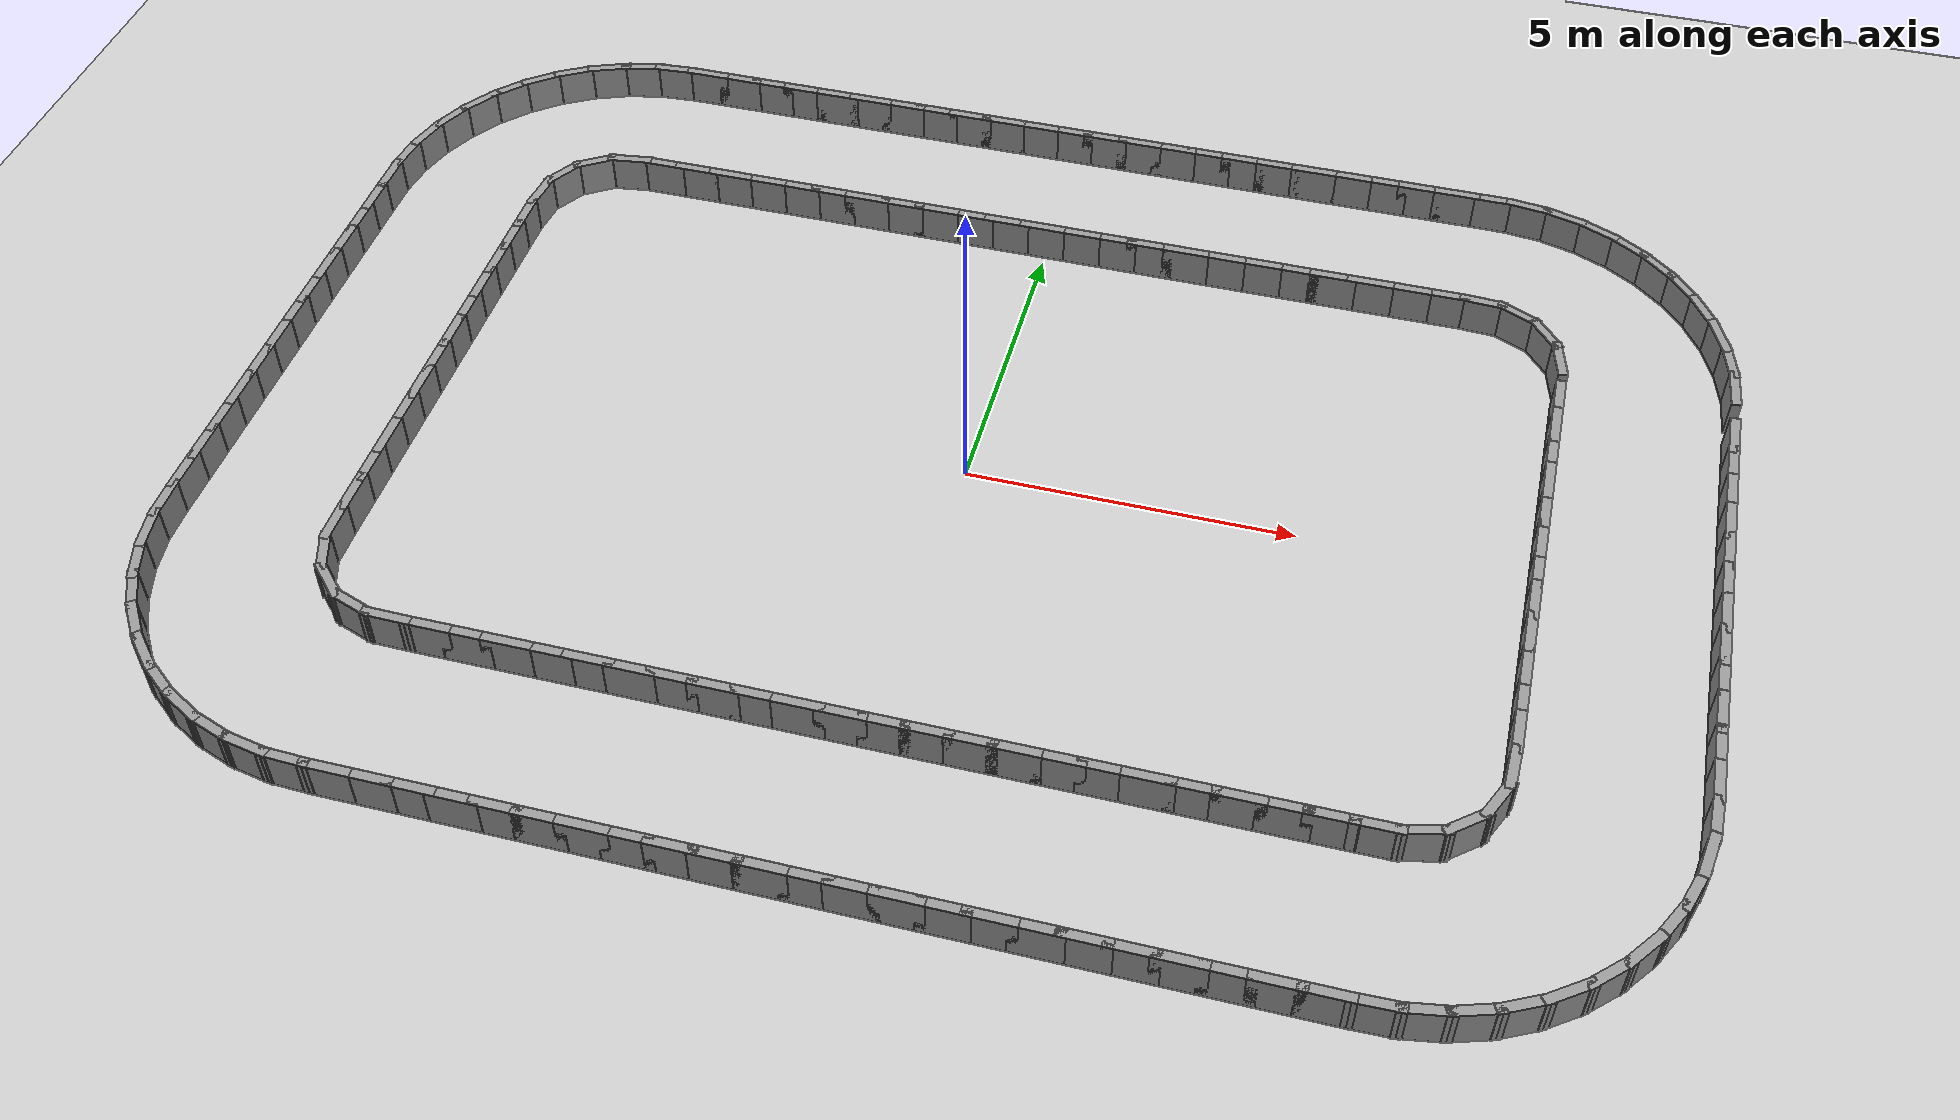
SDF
<?xml version="1.0" ?>
<sdf version='1.7'>
  <world name='default'>
    <plugin name='gazebo_ros_state' filename='libgazebo_ros_state.so'>
      <ros>
        <namespace>/</namespace>
      </ros>
      <update_rate>1000.0</update_rate>
    </plugin>

    <light name='sun' type='directional'>
      <cast_shadows>1</cast_shadows>
      <pose>0 0 10 0 -0 0</pose>
      <diffuse>0.8 0.8 0.8 1</diffuse>
      <specular>0.2 0.2 0.2 1</specular>
      <attenuation>
        <range>1000</range>
        <constant>0.9</constant>
        <linear>0.01</linear>
        <quadratic>0.001</quadratic>
      </attenuation>
      <direction>-0.5 0.1 -0.9</direction>
      <spot>
        <inner_angle>0</inner_angle>
        <outer_angle>0</outer_angle>
        <falloff>0</falloff>
      </spot>
    </light>
    <model name='ground_plane'>
      <static>1</static>
      <link name='link'>
        <collision name='collision'>
          <geometry>
            <plane>
              <normal>0 0 1</normal>
              <size>100 100</size>
            </plane>
          </geometry>
          <surface>
            <friction>
              <ode>
                <mu>100</mu>
                <mu2>50</mu2>
              </ode>
              <torsional>
                <ode/>
              </torsional>
            </friction>
            <contact>
              <ode/>
            </contact>
            <bounce/>
          </surface>
          <max_contacts>10</max_contacts>
        </collision>
        <visual name='visual'>
          <cast_shadows>0</cast_shadows>
          <geometry>
            <plane>
              <normal>0 0 1</normal>
              <size>100 100</size>
            </plane>
          </geometry>
          <material>
            <script>
              <uri>file://media/materials/scripts/gazebo.material</uri>
              <name>Gazebo/Grey</name>
            </script>
          </material>
        </visual>
        <self_collide>0</self_collide>
        <enable_wind>0</enable_wind>
        <kinematic>0</kinematic>
      </link>
    </model>
    <gravity>0 0 -9.8</gravity>
    <magnetic_field>6e-06 2.3e-05 -4.2e-05</magnetic_field>
    <atmosphere type='adiabatic'/>
    <physics type='ode'>
      <max_step_size>0.001</max_step_size>
      <real_time_factor>1</real_time_factor>
      <real_time_update_rate>1000</real_time_update_rate>
    </physics>
    <scene>
      <ambient>0.4 0.4 0.4 1</ambient>
      <background>0.7 0.7 0.7 1</background>
      <shadows>1</shadows>
    </scene>
    <audio>
      <device>default</device>
    </audio>
    <wind/>
    <spherical_coordinates>
      <surface_model>EARTH_WGS84</surface_model>
      <latitude_deg>0</latitude_deg>
      <longitude_deg>0</longitude_deg>
      <elevation>0</elevation>
      <heading_deg>0</heading_deg>
    </spherical_coordinates>
  <model name='rand_rrect_02'>
    <pose>0 0 0 0 -0 0</pose>
    <link name='Wall_0'>
      <collision name='Wall_0_Collision'>
        <geometry><box><size>0.7450 0.1500 0.6000</size></box></geometry>
        <pose>0 0 0.3000 0 -0 0</pose>
      </collision>
      <visual name='Wall_0_Visual'>
        <pose>0 0 0.3000 0 -0 0</pose>
        <geometry><box><size>0.7450 0.1500 0.6000</size></box></geometry>
        <material>
          <script>
            <uri>file://media/materials/scripts/gazebo.material</uri>
            <name>Gazebo/Grey</name>
          </script>
          <ambient>1 1 1 1</ambient>
        </material>
      </visual>
      <pose>8.3819 4.1988 0 0 -0 1.79474</pose>
    </link>
    <link name='Wall_1'>
      <collision name='Wall_1_Collision'>
        <geometry><box><size>0.7450 0.1500 0.6000</size></box></geometry>
        <pose>0 0 0.3000 0 -0 0</pose>
      </collision>
      <visual name='Wall_1_Visual'>
        <pose>0 0 0.3000 0 -0 0</pose>
        <geometry><box><size>0.7450 0.1500 0.6000</size></box></geometry>
        <material>
          <script>
            <uri>file://media/materials/scripts/gazebo.material</uri>
            <name>Gazebo/Grey</name>
          </script>
          <ambient>1 1 1 1</ambient>
        </material>
      </visual>
      <pose>8.1306 4.7217 0 0 -0 2.24261</pose>
    </link>
    <link name='Wall_2'>
      <collision name='Wall_2_Collision'>
        <geometry><box><size>0.7450 0.1500 0.6000</size></box></geometry>
        <pose>0 0 0.3000 0 -0 0</pose>
      </collision>
      <visual name='Wall_2_Visual'>
        <pose>0 0 0.3000 0 -0 0</pose>
        <geometry><box><size>0.7450 0.1500 0.6000</size></box></geometry>
        <material>
          <script>
            <uri>file://media/materials/scripts/gazebo.material</uri>
            <name>Gazebo/Grey</name>
          </script>
          <ambient>1 1 1 1</ambient>
        </material>
      </visual>
      <pose>7.6777 5.0842 0 0 -0 2.69049</pose>
    </link>
    <link name='Wall_3'>
      <collision name='Wall_3_Collision'>
        <geometry><box><size>0.7484 0.1500 0.6000</size></box></geometry>
        <pose>0 0 0.3000 0 -0 0</pose>
      </collision>
      <visual name='Wall_3_Visual'>
        <pose>0 0 0.3000 0 -0 0</pose>
        <geometry><box><size>0.7484 0.1500 0.6000</size></box></geometry>
        <material>
          <script>
            <uri>file://media/materials/scripts/gazebo.material</uri>
            <name>Gazebo/Grey</name>
          </script>
          <ambient>1 1 1 1</ambient>
        </material>
      </visual>
      <pose>7.1113 5.2311 0 0 -0 3.08404</pose>
    </link>
    <link name='Wall_4'>
      <collision name='Wall_4_Collision'>
        <geometry><box><size>0.7500 0.1500 0.6000</size></box></geometry>
        <pose>0 0 0.3000 0 -0 0</pose>
      </collision>
      <visual name='Wall_4_Visual'>
        <pose>0 0 0.3000 0 -0 0</pose>
        <geometry><box><size>0.7500 0.1500 0.6000</size></box></geometry>
        <material>
          <script>
            <uri>file://media/materials/scripts/gazebo.material</uri>
            <name>Gazebo/Grey</name>
          </script>
          <ambient>1 1 1 1</ambient>
        </material>
      </visual>
      <pose>6.5126 5.2483 0 0 -0 3.14159</pose>
    </link>
    <link name='Wall_5'>
      <collision name='Wall_5_Collision'>
        <geometry><box><size>0.7500 0.1500 0.6000</size></box></geometry>
        <pose>0 0 0.3000 0 -0 0</pose>
      </collision>
      <visual name='Wall_5_Visual'>
        <pose>0 0 0.3000 0 -0 0</pose>
        <geometry><box><size>0.7500 0.1500 0.6000</size></box></geometry>
        <material>
          <script>
            <uri>file://media/materials/scripts/gazebo.material</uri>
            <name>Gazebo/Grey</name>
          </script>
          <ambient>1 1 1 1</ambient>
        </material>
      </visual>
      <pose>5.9126 5.2483 0 0 -0 3.14159</pose>
    </link>
    <link name='Wall_6'>
      <collision name='Wall_6_Collision'>
        <geometry><box><size>0.7500 0.1500 0.6000</size></box></geometry>
        <pose>0 0 0.3000 0 -0 0</pose>
      </collision>
      <visual name='Wall_6_Visual'>
        <pose>0 0 0.3000 0 -0 0</pose>
        <geometry><box><size>0.7500 0.1500 0.6000</size></box></geometry>
        <material>
          <script>
            <uri>file://media/materials/scripts/gazebo.material</uri>
            <name>Gazebo/Grey</name>
          </script>
          <ambient>1 1 1 1</ambient>
        </material>
      </visual>
      <pose>5.3126 5.2483 0 0 -0 3.14159</pose>
    </link>
    <link name='Wall_7'>
      <collision name='Wall_7_Collision'>
        <geometry><box><size>0.7500 0.1500 0.6000</size></box></geometry>
        <pose>0 0 0.3000 0 -0 0</pose>
      </collision>
      <visual name='Wall_7_Visual'>
        <pose>0 0 0.3000 0 -0 0</pose>
        <geometry><box><size>0.7500 0.1500 0.6000</size></box></geometry>
        <material>
          <script>
            <uri>file://media/materials/scripts/gazebo.material</uri>
            <name>Gazebo/Grey</name>
          </script>
          <ambient>1 1 1 1</ambient>
        </material>
      </visual>
      <pose>4.7126 5.2483 0 0 -0 3.14159</pose>
    </link>
    <link name='Wall_8'>
      <collision name='Wall_8_Collision'>
        <geometry><box><size>0.7500 0.1500 0.6000</size></box></geometry>
        <pose>0 0 0.3000 0 -0 0</pose>
      </collision>
      <visual name='Wall_8_Visual'>
        <pose>0 0 0.3000 0 -0 0</pose>
        <geometry><box><size>0.7500 0.1500 0.6000</size></box></geometry>
        <material>
          <script>
            <uri>file://media/materials/scripts/gazebo.material</uri>
            <name>Gazebo/Grey</name>
          </script>
          <ambient>1 1 1 1</ambient>
        </material>
      </visual>
      <pose>4.1126 5.2483 0 0 -0 3.14159</pose>
    </link>
    <link name='Wall_9'>
      <collision name='Wall_9_Collision'>
        <geometry><box><size>0.7500 0.1500 0.6000</size></box></geometry>
        <pose>0 0 0.3000 0 -0 0</pose>
      </collision>
      <visual name='Wall_9_Visual'>
        <pose>0 0 0.3000 0 -0 0</pose>
        <geometry><box><size>0.7500 0.1500 0.6000</size></box></geometry>
        <material>
          <script>
            <uri>file://media/materials/scripts/gazebo.material</uri>
            <name>Gazebo/Grey</name>
          </script>
          <ambient>1 1 1 1</ambient>
        </material>
      </visual>
      <pose>3.5126 5.2483 0 0 -0 3.14159</pose>
    </link>
    <link name='Wall_10'>
      <collision name='Wall_10_Collision'>
        <geometry><box><size>0.7500 0.1500 0.6000</size></box></geometry>
        <pose>0 0 0.3000 0 -0 0</pose>
      </collision>
      <visual name='Wall_10_Visual'>
        <pose>0 0 0.3000 0 -0 0</pose>
        <geometry><box><size>0.7500 0.1500 0.6000</size></box></geometry>
        <material>
          <script>
            <uri>file://media/materials/scripts/gazebo.material</uri>
            <name>Gazebo/Grey</name>
          </script>
          <ambient>1 1 1 1</ambient>
        </material>
      </visual>
      <pose>2.9126 5.2483 0 0 -0 3.14159</pose>
    </link>
    <link name='Wall_11'>
      <collision name='Wall_11_Collision'>
        <geometry><box><size>0.7500 0.1500 0.6000</size></box></geometry>
        <pose>0 0 0.3000 0 -0 0</pose>
      </collision>
      <visual name='Wall_11_Visual'>
        <pose>0 0 0.3000 0 -0 0</pose>
        <geometry><box><size>0.7500 0.1500 0.6000</size></box></geometry>
        <material>
          <script>
            <uri>file://media/materials/scripts/gazebo.material</uri>
            <name>Gazebo/Grey</name>
          </script>
          <ambient>1 1 1 1</ambient>
        </material>
      </visual>
      <pose>2.3126 5.2483 0 0 -0 3.14159</pose>
    </link>
    <link name='Wall_12'>
      <collision name='Wall_12_Collision'>
        <geometry><box><size>0.7500 0.1500 0.6000</size></box></geometry>
        <pose>0 0 0.3000 0 -0 0</pose>
      </collision>
      <visual name='Wall_12_Visual'>
        <pose>0 0 0.3000 0 -0 0</pose>
        <geometry><box><size>0.7500 0.1500 0.6000</size></box></geometry>
        <material>
          <script>
            <uri>file://media/materials/scripts/gazebo.material</uri>
            <name>Gazebo/Grey</name>
          </script>
          <ambient>1 1 1 1</ambient>
        </material>
      </visual>
      <pose>1.7126 5.2483 0 0 -0 3.14159</pose>
    </link>
    <link name='Wall_13'>
      <collision name='Wall_13_Collision'>
        <geometry><box><size>0.7500 0.1500 0.6000</size></box></geometry>
        <pose>0 0 0.3000 0 -0 0</pose>
      </collision>
      <visual name='Wall_13_Visual'>
        <pose>0 0 0.3000 0 -0 0</pose>
        <geometry><box><size>0.7500 0.1500 0.6000</size></box></geometry>
        <material>
          <script>
            <uri>file://media/materials/scripts/gazebo.material</uri>
            <name>Gazebo/Grey</name>
          </script>
          <ambient>1 1 1 1</ambient>
        </material>
      </visual>
      <pose>1.1126 5.2483 0 0 -0 3.14159</pose>
    </link>
    <link name='Wall_14'>
      <collision name='Wall_14_Collision'>
        <geometry><box><size>0.7500 0.1500 0.6000</size></box></geometry>
        <pose>0 0 0.3000 0 -0 0</pose>
      </collision>
      <visual name='Wall_14_Visual'>
        <pose>0 0 0.3000 0 -0 0</pose>
        <geometry><box><size>0.7500 0.1500 0.6000</size></box></geometry>
        <material>
          <script>
            <uri>file://media/materials/scripts/gazebo.material</uri>
            <name>Gazebo/Grey</name>
          </script>
          <ambient>1 1 1 1</ambient>
        </material>
      </visual>
      <pose>0.5126 5.2483 0 0 -0 3.14159</pose>
    </link>
    <link name='Wall_15'>
      <collision name='Wall_15_Collision'>
        <geometry><box><size>0.7500 0.1500 0.6000</size></box></geometry>
        <pose>0 0 0.3000 0 -0 0</pose>
      </collision>
      <visual name='Wall_15_Visual'>
        <pose>0 0 0.3000 0 -0 0</pose>
        <geometry><box><size>0.7500 0.1500 0.6000</size></box></geometry>
        <material>
          <script>
            <uri>file://media/materials/scripts/gazebo.material</uri>
            <name>Gazebo/Grey</name>
          </script>
          <ambient>1 1 1 1</ambient>
        </material>
      </visual>
      <pose>-0.0874 5.2483 0 0 -0 3.14159</pose>
    </link>
    <link name='Wall_16'>
      <collision name='Wall_16_Collision'>
        <geometry><box><size>0.7500 0.1500 0.6000</size></box></geometry>
        <pose>0 0 0.3000 0 -0 0</pose>
      </collision>
      <visual name='Wall_16_Visual'>
        <pose>0 0 0.3000 0 -0 0</pose>
        <geometry><box><size>0.7500 0.1500 0.6000</size></box></geometry>
        <material>
          <script>
            <uri>file://media/materials/scripts/gazebo.material</uri>
            <name>Gazebo/Grey</name>
          </script>
          <ambient>1 1 1 1</ambient>
        </material>
      </visual>
      <pose>-0.6874 5.2483 0 0 -0 3.14159</pose>
    </link>
    <link name='Wall_17'>
      <collision name='Wall_17_Collision'>
        <geometry><box><size>0.7500 0.1500 0.6000</size></box></geometry>
        <pose>0 0 0.3000 0 -0 0</pose>
      </collision>
      <visual name='Wall_17_Visual'>
        <pose>0 0 0.3000 0 -0 0</pose>
        <geometry><box><size>0.7500 0.1500 0.6000</size></box></geometry>
        <material>
          <script>
            <uri>file://media/materials/scripts/gazebo.material</uri>
            <name>Gazebo/Grey</name>
          </script>
          <ambient>1 1 1 1</ambient>
        </material>
      </visual>
      <pose>-1.2874 5.2483 0 0 -0 3.14159</pose>
    </link>
    <link name='Wall_18'>
      <collision name='Wall_18_Collision'>
        <geometry><box><size>0.7500 0.1500 0.6000</size></box></geometry>
        <pose>0 0 0.3000 0 -0 0</pose>
      </collision>
      <visual name='Wall_18_Visual'>
        <pose>0 0 0.3000 0 -0 0</pose>
        <geometry><box><size>0.7500 0.1500 0.6000</size></box></geometry>
        <material>
          <script>
            <uri>file://media/materials/scripts/gazebo.material</uri>
            <name>Gazebo/Grey</name>
          </script>
          <ambient>1 1 1 1</ambient>
        </material>
      </visual>
      <pose>-1.8874 5.2483 0 0 -0 3.14159</pose>
    </link>
    <link name='Wall_19'>
      <collision name='Wall_19_Collision'>
        <geometry><box><size>0.7500 0.1500 0.6000</size></box></geometry>
        <pose>0 0 0.3000 0 -0 0</pose>
      </collision>
      <visual name='Wall_19_Visual'>
        <pose>0 0 0.3000 0 -0 0</pose>
        <geometry><box><size>0.7500 0.1500 0.6000</size></box></geometry>
        <material>
          <script>
            <uri>file://media/materials/scripts/gazebo.material</uri>
            <name>Gazebo/Grey</name>
          </script>
          <ambient>1 1 1 1</ambient>
        </material>
      </visual>
      <pose>-2.4874 5.2483 0 0 -0 3.14159</pose>
    </link>
    <link name='Wall_20'>
      <collision name='Wall_20_Collision'>
        <geometry><box><size>0.7500 0.1500 0.6000</size></box></geometry>
        <pose>0 0 0.3000 0 -0 0</pose>
      </collision>
      <visual name='Wall_20_Visual'>
        <pose>0 0 0.3000 0 -0 0</pose>
        <geometry><box><size>0.7500 0.1500 0.6000</size></box></geometry>
        <material>
          <script>
            <uri>file://media/materials/scripts/gazebo.material</uri>
            <name>Gazebo/Grey</name>
          </script>
          <ambient>1 1 1 1</ambient>
        </material>
      </visual>
      <pose>-3.0874 5.2483 0 0 -0 3.14159</pose>
    </link>
    <link name='Wall_21'>
      <collision name='Wall_21_Collision'>
        <geometry><box><size>0.7500 0.1500 0.6000</size></box></geometry>
        <pose>0 0 0.3000 0 -0 0</pose>
      </collision>
      <visual name='Wall_21_Visual'>
        <pose>0 0 0.3000 0 -0 0</pose>
        <geometry><box><size>0.7500 0.1500 0.6000</size></box></geometry>
        <material>
          <script>
            <uri>file://media/materials/scripts/gazebo.material</uri>
            <name>Gazebo/Grey</name>
          </script>
          <ambient>1 1 1 1</ambient>
        </material>
      </visual>
      <pose>-3.6874 5.2483 0 0 -0 3.14159</pose>
    </link>
    <link name='Wall_22'>
      <collision name='Wall_22_Collision'>
        <geometry><box><size>0.7500 0.1500 0.6000</size></box></geometry>
        <pose>0 0 0.3000 0 -0 0</pose>
      </collision>
      <visual name='Wall_22_Visual'>
        <pose>0 0 0.3000 0 -0 0</pose>
        <geometry><box><size>0.7500 0.1500 0.6000</size></box></geometry>
        <material>
          <script>
            <uri>file://media/materials/scripts/gazebo.material</uri>
            <name>Gazebo/Grey</name>
          </script>
          <ambient>1 1 1 1</ambient>
        </material>
      </visual>
      <pose>-4.2874 5.2483 0 0 -0 3.14159</pose>
    </link>
    <link name='Wall_23'>
      <collision name='Wall_23_Collision'>
        <geometry><box><size>0.7500 0.1500 0.6000</size></box></geometry>
        <pose>0 0 0.3000 0 -0 0</pose>
      </collision>
      <visual name='Wall_23_Visual'>
        <pose>0 0 0.3000 0 -0 0</pose>
        <geometry><box><size>0.7500 0.1500 0.6000</size></box></geometry>
        <material>
          <script>
            <uri>file://media/materials/scripts/gazebo.material</uri>
            <name>Gazebo/Grey</name>
          </script>
          <ambient>1 1 1 1</ambient>
        </material>
      </visual>
      <pose>-4.8874 5.2483 0 0 -0 3.14159</pose>
    </link>
    <link name='Wall_24'>
      <collision name='Wall_24_Collision'>
        <geometry><box><size>0.7500 0.1500 0.6000</size></box></geometry>
        <pose>0 0 0.3000 0 -0 0</pose>
      </collision>
      <visual name='Wall_24_Visual'>
        <pose>0 0 0.3000 0 -0 0</pose>
        <geometry><box><size>0.7500 0.1500 0.6000</size></box></geometry>
        <material>
          <script>
            <uri>file://media/materials/scripts/gazebo.material</uri>
            <name>Gazebo/Grey</name>
          </script>
          <ambient>1 1 1 1</ambient>
        </material>
      </visual>
      <pose>-5.4874 5.2483 0 0 -0 3.14159</pose>
    </link>
    <link name='Wall_25'>
      <collision name='Wall_25_Collision'>
        <geometry><box><size>0.7500 0.1500 0.6000</size></box></geometry>
        <pose>0 0 0.3000 0 -0 0</pose>
      </collision>
      <visual name='Wall_25_Visual'>
        <pose>0 0 0.3000 0 -0 0</pose>
        <geometry><box><size>0.7500 0.1500 0.6000</size></box></geometry>
        <material>
          <script>
            <uri>file://media/materials/scripts/gazebo.material</uri>
            <name>Gazebo/Grey</name>
          </script>
          <ambient>1 1 1 1</ambient>
        </material>
      </visual>
      <pose>-6.0874 5.2483 0 0 -0 3.14159</pose>
    </link>
    <link name='Wall_26'>
      <collision name='Wall_26_Collision'>
        <geometry><box><size>0.7500 0.1500 0.6000</size></box></geometry>
        <pose>0 0 0.3000 0 -0 0</pose>
      </collision>
      <visual name='Wall_26_Visual'>
        <pose>0 0 0.3000 0 -0 0</pose>
        <geometry><box><size>0.7500 0.1500 0.6000</size></box></geometry>
        <material>
          <script>
            <uri>file://media/materials/scripts/gazebo.material</uri>
            <name>Gazebo/Grey</name>
          </script>
          <ambient>1 1 1 1</ambient>
        </material>
      </visual>
      <pose>-6.6874 5.2483 0 0 -0 3.14159</pose>
    </link>
    <link name='Wall_27'>
      <collision name='Wall_27_Collision'>
        <geometry><box><size>0.7459 0.1500 0.6000</size></box></geometry>
        <pose>0 0 0.3000 0 -0 0</pose>
      </collision>
      <visual name='Wall_27_Visual'>
        <pose>0 0 0.3000 0 -0 0</pose>
        <geometry><box><size>0.7459 0.1500 0.6000</size></box></geometry>
        <material>
          <script>
            <uri>file://media/materials/scripts/gazebo.material</uri>
            <name>Gazebo/Grey</name>
          </script>
          <ambient>1 1 1 1</ambient>
        </material>
      </visual>
      <pose>-7.2823 5.2060 0 0 -0 -2.99887</pose>
    </link>
    <link name='Wall_28'>
      <collision name='Wall_28_Collision'>
        <geometry><box><size>0.7450 0.1500 0.6000</size></box></geometry>
        <pose>0 0 0.3000 0 -0 0</pose>
      </collision>
      <visual name='Wall_28_Visual'>
        <pose>0 0 0.3000 0 -0 0</pose>
        <geometry><box><size>0.7450 0.1500 0.6000</size></box></geometry>
        <material>
          <script>
            <uri>file://media/materials/scripts/gazebo.material</uri>
            <name>Gazebo/Grey</name>
          </script>
          <ambient>1 1 1 1</ambient>
        </material>
      </visual>
      <pose>-7.8258 5.0002 0 0 -0 -2.56004</pose>
    </link>
    <link name='Wall_29'>
      <collision name='Wall_29_Collision'>
        <geometry><box><size>0.7450 0.1500 0.6000</size></box></geometry>
        <pose>0 0 0.3000 0 -0 0</pose>
      </collision>
      <visual name='Wall_29_Visual'>
        <pose>0 0 0.3000 0 -0 0</pose>
        <geometry><box><size>0.7450 0.1500 0.6000</size></box></geometry>
        <material>
          <script>
            <uri>file://media/materials/scripts/gazebo.material</uri>
            <name>Gazebo/Grey</name>
          </script>
          <ambient>1 1 1 1</ambient>
        </material>
      </visual>
      <pose>-8.2277 4.5818 0 0 -0 -2.11215</pose>
    </link>
    <link name='Wall_30'>
      <collision name='Wall_30_Collision'>
        <geometry><box><size>0.7467 0.1500 0.6000</size></box></geometry>
        <pose>0 0 0.3000 0 -0 0</pose>
      </collision>
      <visual name='Wall_30_Visual'>
        <pose>0 0 0.3000 0 -0 0</pose>
        <geometry><box><size>0.7467 0.1500 0.6000</size></box></geometry>
        <material>
          <script>
            <uri>file://media/materials/scripts/gazebo.material</uri>
            <name>Gazebo/Grey</name>
          </script>
          <ambient>1 1 1 1</ambient>
        </material>
      </visual>
      <pose>-8.4145 4.0304 0 0 -0 -1.68320</pose>
    </link>
    <link name='Wall_31'>
      <collision name='Wall_31_Collision'>
        <geometry><box><size>0.7500 0.1500 0.6000</size></box></geometry>
        <pose>0 0 0.3000 0 -0 0</pose>
      </collision>
      <visual name='Wall_31_Visual'>
        <pose>0 0 0.3000 0 -0 0</pose>
        <geometry><box><size>0.7500 0.1500 0.6000</size></box></geometry>
        <material>
          <script>
            <uri>file://media/materials/scripts/gazebo.material</uri>
            <name>Gazebo/Grey</name>
          </script>
          <ambient>1 1 1 1</ambient>
        </material>
      </visual>
      <pose>-8.4479 3.4339 0 0 -0 -1.57080</pose>
    </link>
    <link name='Wall_32'>
      <collision name='Wall_32_Collision'>
        <geometry><box><size>0.7500 0.1500 0.6000</size></box></geometry>
        <pose>0 0 0.3000 0 -0 0</pose>
      </collision>
      <visual name='Wall_32_Visual'>
        <pose>0 0 0.3000 0 -0 0</pose>
        <geometry><box><size>0.7500 0.1500 0.6000</size></box></geometry>
        <material>
          <script>
            <uri>file://media/materials/scripts/gazebo.material</uri>
            <name>Gazebo/Grey</name>
          </script>
          <ambient>1 1 1 1</ambient>
        </material>
      </visual>
      <pose>-8.4479 2.8339 0 0 -0 -1.57080</pose>
    </link>
    <link name='Wall_33'>
      <collision name='Wall_33_Collision'>
        <geometry><box><size>0.7500 0.1500 0.6000</size></box></geometry>
        <pose>0 0 0.3000 0 -0 0</pose>
      </collision>
      <visual name='Wall_33_Visual'>
        <pose>0 0 0.3000 0 -0 0</pose>
        <geometry><box><size>0.7500 0.1500 0.6000</size></box></geometry>
        <material>
          <script>
            <uri>file://media/materials/scripts/gazebo.material</uri>
            <name>Gazebo/Grey</name>
          </script>
          <ambient>1 1 1 1</ambient>
        </material>
      </visual>
      <pose>-8.4479 2.2339 0 0 -0 -1.57080</pose>
    </link>
    <link name='Wall_34'>
      <collision name='Wall_34_Collision'>
        <geometry><box><size>0.7500 0.1500 0.6000</size></box></geometry>
        <pose>0 0 0.3000 0 -0 0</pose>
      </collision>
      <visual name='Wall_34_Visual'>
        <pose>0 0 0.3000 0 -0 0</pose>
        <geometry><box><size>0.7500 0.1500 0.6000</size></box></geometry>
        <material>
          <script>
            <uri>file://media/materials/scripts/gazebo.material</uri>
            <name>Gazebo/Grey</name>
          </script>
          <ambient>1 1 1 1</ambient>
        </material>
      </visual>
      <pose>-8.4479 1.6339 0 0 -0 -1.57080</pose>
    </link>
    <link name='Wall_35'>
      <collision name='Wall_35_Collision'>
        <geometry><box><size>0.7500 0.1500 0.6000</size></box></geometry>
        <pose>0 0 0.3000 0 -0 0</pose>
      </collision>
      <visual name='Wall_35_Visual'>
        <pose>0 0 0.3000 0 -0 0</pose>
        <geometry><box><size>0.7500 0.1500 0.6000</size></box></geometry>
        <material>
          <script>
            <uri>file://media/materials/scripts/gazebo.material</uri>
            <name>Gazebo/Grey</name>
          </script>
          <ambient>1 1 1 1</ambient>
        </material>
      </visual>
      <pose>-8.4479 1.0339 0 0 -0 -1.57080</pose>
    </link>
    <link name='Wall_36'>
      <collision name='Wall_36_Collision'>
        <geometry><box><size>0.7500 0.1500 0.6000</size></box></geometry>
        <pose>0 0 0.3000 0 -0 0</pose>
      </collision>
      <visual name='Wall_36_Visual'>
        <pose>0 0 0.3000 0 -0 0</pose>
        <geometry><box><size>0.7500 0.1500 0.6000</size></box></geometry>
        <material>
          <script>
            <uri>file://media/materials/scripts/gazebo.material</uri>
            <name>Gazebo/Grey</name>
          </script>
          <ambient>1 1 1 1</ambient>
        </material>
      </visual>
      <pose>-8.4479 0.4339 0 0 -0 -1.57080</pose>
    </link>
    <link name='Wall_37'>
      <collision name='Wall_37_Collision'>
        <geometry><box><size>0.7500 0.1500 0.6000</size></box></geometry>
        <pose>0 0 0.3000 0 -0 0</pose>
      </collision>
      <visual name='Wall_37_Visual'>
        <pose>0 0 0.3000 0 -0 0</pose>
        <geometry><box><size>0.7500 0.1500 0.6000</size></box></geometry>
        <material>
          <script>
            <uri>file://media/materials/scripts/gazebo.material</uri>
            <name>Gazebo/Grey</name>
          </script>
          <ambient>1 1 1 1</ambient>
        </material>
      </visual>
      <pose>-8.4479 -0.1661 0 0 -0 -1.57080</pose>
    </link>
    <link name='Wall_38'>
      <collision name='Wall_38_Collision'>
        <geometry><box><size>0.7500 0.1500 0.6000</size></box></geometry>
        <pose>0 0 0.3000 0 -0 0</pose>
      </collision>
      <visual name='Wall_38_Visual'>
        <pose>0 0 0.3000 0 -0 0</pose>
        <geometry><box><size>0.7500 0.1500 0.6000</size></box></geometry>
        <material>
          <script>
            <uri>file://media/materials/scripts/gazebo.material</uri>
            <name>Gazebo/Grey</name>
          </script>
          <ambient>1 1 1 1</ambient>
        </material>
      </visual>
      <pose>-8.4479 -0.7661 0 0 -0 -1.57080</pose>
    </link>
    <link name='Wall_39'>
      <collision name='Wall_39_Collision'>
        <geometry><box><size>0.7500 0.1500 0.6000</size></box></geometry>
        <pose>0 0 0.3000 0 -0 0</pose>
      </collision>
      <visual name='Wall_39_Visual'>
        <pose>0 0 0.3000 0 -0 0</pose>
        <geometry><box><size>0.7500 0.1500 0.6000</size></box></geometry>
        <material>
          <script>
            <uri>file://media/materials/scripts/gazebo.material</uri>
            <name>Gazebo/Grey</name>
          </script>
          <ambient>1 1 1 1</ambient>
        </material>
      </visual>
      <pose>-8.4479 -1.3661 0 0 -0 -1.57080</pose>
    </link>
    <link name='Wall_40'>
      <collision name='Wall_40_Collision'>
        <geometry><box><size>0.7500 0.1500 0.6000</size></box></geometry>
        <pose>0 0 0.3000 0 -0 0</pose>
      </collision>
      <visual name='Wall_40_Visual'>
        <pose>0 0 0.3000 0 -0 0</pose>
        <geometry><box><size>0.7500 0.1500 0.6000</size></box></geometry>
        <material>
          <script>
            <uri>file://media/materials/scripts/gazebo.material</uri>
            <name>Gazebo/Grey</name>
          </script>
          <ambient>1 1 1 1</ambient>
        </material>
      </visual>
      <pose>-8.4479 -1.9661 0 0 -0 -1.57080</pose>
    </link>
    <link name='Wall_41'>
      <collision name='Wall_41_Collision'>
        <geometry><box><size>0.7500 0.1500 0.6000</size></box></geometry>
        <pose>0 0 0.3000 0 -0 0</pose>
      </collision>
      <visual name='Wall_41_Visual'>
        <pose>0 0 0.3000 0 -0 0</pose>
        <geometry><box><size>0.7500 0.1500 0.6000</size></box></geometry>
        <material>
          <script>
            <uri>file://media/materials/scripts/gazebo.material</uri>
            <name>Gazebo/Grey</name>
          </script>
          <ambient>1 1 1 1</ambient>
        </material>
      </visual>
      <pose>-8.4479 -2.5661 0 0 -0 -1.57080</pose>
    </link>
    <link name='Wall_42'>
      <collision name='Wall_42_Collision'>
        <geometry><box><size>0.7500 0.1500 0.6000</size></box></geometry>
        <pose>0 0 0.3000 0 -0 0</pose>
      </collision>
      <visual name='Wall_42_Visual'>
        <pose>0 0 0.3000 0 -0 0</pose>
        <geometry><box><size>0.7500 0.1500 0.6000</size></box></geometry>
        <material>
          <script>
            <uri>file://media/materials/scripts/gazebo.material</uri>
            <name>Gazebo/Grey</name>
          </script>
          <ambient>1 1 1 1</ambient>
        </material>
      </visual>
      <pose>-8.4479 -3.1661 0 0 -0 -1.57080</pose>
    </link>
    <link name='Wall_43'>
      <collision name='Wall_43_Collision'>
        <geometry><box><size>0.7497 0.1500 0.6000</size></box></geometry>
        <pose>0 0 0.3000 0 -0 0</pose>
      </collision>
      <visual name='Wall_43_Visual'>
        <pose>0 0 0.3000 0 -0 0</pose>
        <geometry><box><size>0.7497 0.1500 0.6000</size></box></geometry>
        <material>
          <script>
            <uri>file://media/materials/scripts/gazebo.material</uri>
            <name>Gazebo/Grey</name>
          </script>
          <ambient>1 1 1 1</ambient>
        </material>
      </visual>
      <pose>-8.4433 -3.7659 0 0 -0 -1.55539</pose>
    </link>
    <link name='Wall_44'>
      <collision name='Wall_44_Collision'>
        <geometry><box><size>0.7450 0.1500 0.6000</size></box></geometry>
        <pose>0 0 0.3000 0 -0 0</pose>
      </collision>
      <visual name='Wall_44_Visual'>
        <pose>0 0 0.3000 0 -0 0</pose>
        <geometry><box><size>0.7450 0.1500 0.6000</size></box></geometry>
        <material>
          <script>
            <uri>file://media/materials/scripts/gazebo.material</uri>
            <name>Gazebo/Grey</name>
          </script>
          <ambient>1 1 1 1</ambient>
        </material>
      </visual>
      <pose>-8.3391 -4.3460 0 0 -0 -1.22936</pose>
    </link>
    <link name='Wall_45'>
      <collision name='Wall_45_Collision'>
        <geometry><box><size>0.7450 0.1500 0.6000</size></box></geometry>
        <pose>0 0 0.3000 0 -0 0</pose>
      </collision>
      <visual name='Wall_45_Visual'>
        <pose>0 0 0.3000 0 -0 0</pose>
        <geometry><box><size>0.7450 0.1500 0.6000</size></box></geometry>
        <material>
          <script>
            <uri>file://media/materials/scripts/gazebo.material</uri>
            <name>Gazebo/Grey</name>
          </script>
          <ambient>1 1 1 1</ambient>
        </material>
      </visual>
      <pose>-8.0283 -4.8359 0 0 -0 -0.78149</pose>
    </link>
    <link name='Wall_46'>
      <collision name='Wall_46_Collision'>
        <geometry><box><size>0.7450 0.1500 0.6000</size></box></geometry>
        <pose>0 0 0.3000 0 -0 0</pose>
      </collision>
      <visual name='Wall_46_Visual'>
        <pose>0 0 0.3000 0 -0 0</pose>
        <geometry><box><size>0.7450 0.1500 0.6000</size></box></geometry>
        <material>
          <script>
            <uri>file://media/materials/scripts/gazebo.material</uri>
            <name>Gazebo/Grey</name>
          </script>
          <ambient>1 1 1 1</ambient>
        </material>
      </visual>
      <pose>-7.5360 -5.1429 0 0 -0 -0.33360</pose>
    </link>
    <link name='Wall_47'>
      <collision name='Wall_47_Collision'>
        <geometry><box><size>0.7498 0.1500 0.6000</size></box></geometry>
        <pose>0 0 0.3000 0 -0 0</pose>
      </collision>
      <visual name='Wall_47_Visual'>
        <pose>0 0 0.3000 0 -0 0</pose>
        <geometry><box><size>0.7498 0.1500 0.6000</size></box></geometry>
        <material>
          <script>
            <uri>file://media/materials/scripts/gazebo.material</uri>
            <name>Gazebo/Grey</name>
          </script>
          <ambient>1 1 1 1</ambient>
        </material>
      </visual>
      <pose>-6.9551 -5.2443 0 0 -0 -0.01342</pose>
    </link>
    <link name='Wall_48'>
      <collision name='Wall_48_Collision'>
        <geometry><box><size>0.7500 0.1500 0.6000</size></box></geometry>
        <pose>0 0 0.3000 0 -0 0</pose>
      </collision>
      <visual name='Wall_48_Visual'>
        <pose>0 0 0.3000 0 -0 0</pose>
        <geometry><box><size>0.7500 0.1500 0.6000</size></box></geometry>
        <material>
          <script>
            <uri>file://media/materials/scripts/gazebo.material</uri>
            <name>Gazebo/Grey</name>
          </script>
          <ambient>1 1 1 1</ambient>
        </material>
      </visual>
      <pose>-6.3552 -5.2483 0 0 -0 0.00000</pose>
    </link>
    <link name='Wall_49'>
      <collision name='Wall_49_Collision'>
        <geometry><box><size>0.7500 0.1500 0.6000</size></box></geometry>
        <pose>0 0 0.3000 0 -0 0</pose>
      </collision>
      <visual name='Wall_49_Visual'>
        <pose>0 0 0.3000 0 -0 0</pose>
        <geometry><box><size>0.7500 0.1500 0.6000</size></box></geometry>
        <material>
          <script>
            <uri>file://media/materials/scripts/gazebo.material</uri>
            <name>Gazebo/Grey</name>
          </script>
          <ambient>1 1 1 1</ambient>
        </material>
      </visual>
      <pose>-5.7552 -5.2483 0 0 -0 0.00000</pose>
    </link>
    <link name='Wall_50'>
      <collision name='Wall_50_Collision'>
        <geometry><box><size>0.7500 0.1500 0.6000</size></box></geometry>
        <pose>0 0 0.3000 0 -0 0</pose>
      </collision>
      <visual name='Wall_50_Visual'>
        <pose>0 0 0.3000 0 -0 0</pose>
        <geometry><box><size>0.7500 0.1500 0.6000</size></box></geometry>
        <material>
          <script>
            <uri>file://media/materials/scripts/gazebo.material</uri>
            <name>Gazebo/Grey</name>
          </script>
          <ambient>1 1 1 1</ambient>
        </material>
      </visual>
      <pose>-5.1552 -5.2483 0 0 -0 0.00000</pose>
    </link>
    <link name='Wall_51'>
      <collision name='Wall_51_Collision'>
        <geometry><box><size>0.7500 0.1500 0.6000</size></box></geometry>
        <pose>0 0 0.3000 0 -0 0</pose>
      </collision>
      <visual name='Wall_51_Visual'>
        <pose>0 0 0.3000 0 -0 0</pose>
        <geometry><box><size>0.7500 0.1500 0.6000</size></box></geometry>
        <material>
          <script>
            <uri>file://media/materials/scripts/gazebo.material</uri>
            <name>Gazebo/Grey</name>
          </script>
          <ambient>1 1 1 1</ambient>
        </material>
      </visual>
      <pose>-4.5552 -5.2483 0 0 -0 0.00000</pose>
    </link>
    <link name='Wall_52'>
      <collision name='Wall_52_Collision'>
        <geometry><box><size>0.7500 0.1500 0.6000</size></box></geometry>
        <pose>0 0 0.3000 0 -0 0</pose>
      </collision>
      <visual name='Wall_52_Visual'>
        <pose>0 0 0.3000 0 -0 0</pose>
        <geometry><box><size>0.7500 0.1500 0.6000</size></box></geometry>
        <material>
          <script>
            <uri>file://media/materials/scripts/gazebo.material</uri>
            <name>Gazebo/Grey</name>
          </script>
          <ambient>1 1 1 1</ambient>
        </material>
      </visual>
      <pose>-3.9552 -5.2483 0 0 -0 0.00000</pose>
    </link>
    <link name='Wall_53'>
      <collision name='Wall_53_Collision'>
        <geometry><box><size>0.7500 0.1500 0.6000</size></box></geometry>
        <pose>0 0 0.3000 0 -0 0</pose>
      </collision>
      <visual name='Wall_53_Visual'>
        <pose>0 0 0.3000 0 -0 0</pose>
        <geometry><box><size>0.7500 0.1500 0.6000</size></box></geometry>
        <material>
          <script>
            <uri>file://media/materials/scripts/gazebo.material</uri>
            <name>Gazebo/Grey</name>
          </script>
          <ambient>1 1 1 1</ambient>
        </material>
      </visual>
      <pose>-3.3552 -5.2483 0 0 -0 0.00000</pose>
    </link>
    <link name='Wall_54'>
      <collision name='Wall_54_Collision'>
        <geometry><box><size>0.7500 0.1500 0.6000</size></box></geometry>
        <pose>0 0 0.3000 0 -0 0</pose>
      </collision>
      <visual name='Wall_54_Visual'>
        <pose>0 0 0.3000 0 -0 0</pose>
        <geometry><box><size>0.7500 0.1500 0.6000</size></box></geometry>
        <material>
          <script>
            <uri>file://media/materials/scripts/gazebo.material</uri>
            <name>Gazebo/Grey</name>
          </script>
          <ambient>1 1 1 1</ambient>
        </material>
      </visual>
      <pose>-2.7552 -5.2483 0 0 -0 0.00000</pose>
    </link>
    <link name='Wall_55'>
      <collision name='Wall_55_Collision'>
        <geometry><box><size>0.7500 0.1500 0.6000</size></box></geometry>
        <pose>0 0 0.3000 0 -0 0</pose>
      </collision>
      <visual name='Wall_55_Visual'>
        <pose>0 0 0.3000 0 -0 0</pose>
        <geometry><box><size>0.7500 0.1500 0.6000</size></box></geometry>
        <material>
          <script>
            <uri>file://media/materials/scripts/gazebo.material</uri>
            <name>Gazebo/Grey</name>
          </script>
          <ambient>1 1 1 1</ambient>
        </material>
      </visual>
      <pose>-2.1552 -5.2483 0 0 -0 0.00000</pose>
    </link>
    <link name='Wall_56'>
      <collision name='Wall_56_Collision'>
        <geometry><box><size>0.7500 0.1500 0.6000</size></box></geometry>
        <pose>0 0 0.3000 0 -0 0</pose>
      </collision>
      <visual name='Wall_56_Visual'>
        <pose>0 0 0.3000 0 -0 0</pose>
        <geometry><box><size>0.7500 0.1500 0.6000</size></box></geometry>
        <material>
          <script>
            <uri>file://media/materials/scripts/gazebo.material</uri>
            <name>Gazebo/Grey</name>
          </script>
          <ambient>1 1 1 1</ambient>
        </material>
      </visual>
      <pose>-1.5552 -5.2483 0 0 -0 0.00000</pose>
    </link>
    <link name='Wall_57'>
      <collision name='Wall_57_Collision'>
        <geometry><box><size>0.7500 0.1500 0.6000</size></box></geometry>
        <pose>0 0 0.3000 0 -0 0</pose>
      </collision>
      <visual name='Wall_57_Visual'>
        <pose>0 0 0.3000 0 -0 0</pose>
        <geometry><box><size>0.7500 0.1500 0.6000</size></box></geometry>
        <material>
          <script>
            <uri>file://media/materials/scripts/gazebo.material</uri>
            <name>Gazebo/Grey</name>
          </script>
          <ambient>1 1 1 1</ambient>
        </material>
      </visual>
      <pose>-0.9552 -5.2483 0 0 -0 0.00000</pose>
    </link>
    <link name='Wall_58'>
      <collision name='Wall_58_Collision'>
        <geometry><box><size>0.7500 0.1500 0.6000</size></box></geometry>
        <pose>0 0 0.3000 0 -0 0</pose>
      </collision>
      <visual name='Wall_58_Visual'>
        <pose>0 0 0.3000 0 -0 0</pose>
        <geometry><box><size>0.7500 0.1500 0.6000</size></box></geometry>
        <material>
          <script>
            <uri>file://media/materials/scripts/gazebo.material</uri>
            <name>Gazebo/Grey</name>
          </script>
          <ambient>1 1 1 1</ambient>
        </material>
      </visual>
      <pose>-0.3552 -5.2483 0 0 -0 0.00000</pose>
    </link>
    <link name='Wall_59'>
      <collision name='Wall_59_Collision'>
        <geometry><box><size>0.7500 0.1500 0.6000</size></box></geometry>
        <pose>0 0 0.3000 0 -0 0</pose>
      </collision>
      <visual name='Wall_59_Visual'>
        <pose>0 0 0.3000 0 -0 0</pose>
        <geometry><box><size>0.7500 0.1500 0.6000</size></box></geometry>
        <material>
          <script>
            <uri>file://media/materials/scripts/gazebo.material</uri>
            <name>Gazebo/Grey</name>
          </script>
          <ambient>1 1 1 1</ambient>
        </material>
      </visual>
      <pose>0.2448 -5.2483 0 0 -0 0.00000</pose>
    </link>
    <link name='Wall_60'>
      <collision name='Wall_60_Collision'>
        <geometry><box><size>0.7500 0.1500 0.6000</size></box></geometry>
        <pose>0 0 0.3000 0 -0 0</pose>
      </collision>
      <visual name='Wall_60_Visual'>
        <pose>0 0 0.3000 0 -0 0</pose>
        <geometry><box><size>0.7500 0.1500 0.6000</size></box></geometry>
        <material>
          <script>
            <uri>file://media/materials/scripts/gazebo.material</uri>
            <name>Gazebo/Grey</name>
          </script>
          <ambient>1 1 1 1</ambient>
        </material>
      </visual>
      <pose>0.8448 -5.2483 0 0 -0 0.00000</pose>
    </link>
    <link name='Wall_61'>
      <collision name='Wall_61_Collision'>
        <geometry><box><size>0.7500 0.1500 0.6000</size></box></geometry>
        <pose>0 0 0.3000 0 -0 0</pose>
      </collision>
      <visual name='Wall_61_Visual'>
        <pose>0 0 0.3000 0 -0 0</pose>
        <geometry><box><size>0.7500 0.1500 0.6000</size></box></geometry>
        <material>
          <script>
            <uri>file://media/materials/scripts/gazebo.material</uri>
            <name>Gazebo/Grey</name>
          </script>
          <ambient>1 1 1 1</ambient>
        </material>
      </visual>
      <pose>1.4448 -5.2483 0 0 -0 0.00000</pose>
    </link>
    <link name='Wall_62'>
      <collision name='Wall_62_Collision'>
        <geometry><box><size>0.7500 0.1500 0.6000</size></box></geometry>
        <pose>0 0 0.3000 0 -0 0</pose>
      </collision>
      <visual name='Wall_62_Visual'>
        <pose>0 0 0.3000 0 -0 0</pose>
        <geometry><box><size>0.7500 0.1500 0.6000</size></box></geometry>
        <material>
          <script>
            <uri>file://media/materials/scripts/gazebo.material</uri>
            <name>Gazebo/Grey</name>
          </script>
          <ambient>1 1 1 1</ambient>
        </material>
      </visual>
      <pose>2.0448 -5.2483 0 0 -0 0.00000</pose>
    </link>
    <link name='Wall_63'>
      <collision name='Wall_63_Collision'>
        <geometry><box><size>0.7500 0.1500 0.6000</size></box></geometry>
        <pose>0 0 0.3000 0 -0 0</pose>
      </collision>
      <visual name='Wall_63_Visual'>
        <pose>0 0 0.3000 0 -0 0</pose>
        <geometry><box><size>0.7500 0.1500 0.6000</size></box></geometry>
        <material>
          <script>
            <uri>file://media/materials/scripts/gazebo.material</uri>
            <name>Gazebo/Grey</name>
          </script>
          <ambient>1 1 1 1</ambient>
        </material>
      </visual>
      <pose>2.6448 -5.2483 0 0 -0 0.00000</pose>
    </link>
    <link name='Wall_64'>
      <collision name='Wall_64_Collision'>
        <geometry><box><size>0.7500 0.1500 0.6000</size></box></geometry>
        <pose>0 0 0.3000 0 -0 0</pose>
      </collision>
      <visual name='Wall_64_Visual'>
        <pose>0 0 0.3000 0 -0 0</pose>
        <geometry><box><size>0.7500 0.1500 0.6000</size></box></geometry>
        <material>
          <script>
            <uri>file://media/materials/scripts/gazebo.material</uri>
            <name>Gazebo/Grey</name>
          </script>
          <ambient>1 1 1 1</ambient>
        </material>
      </visual>
      <pose>3.2448 -5.2483 0 0 -0 0.00000</pose>
    </link>
    <link name='Wall_65'>
      <collision name='Wall_65_Collision'>
        <geometry><box><size>0.7500 0.1500 0.6000</size></box></geometry>
        <pose>0 0 0.3000 0 -0 0</pose>
      </collision>
      <visual name='Wall_65_Visual'>
        <pose>0 0 0.3000 0 -0 0</pose>
        <geometry><box><size>0.7500 0.1500 0.6000</size></box></geometry>
        <material>
          <script>
            <uri>file://media/materials/scripts/gazebo.material</uri>
            <name>Gazebo/Grey</name>
          </script>
          <ambient>1 1 1 1</ambient>
        </material>
      </visual>
      <pose>3.8448 -5.2483 0 0 -0 0.00000</pose>
    </link>
    <link name='Wall_66'>
      <collision name='Wall_66_Collision'>
        <geometry><box><size>0.7500 0.1500 0.6000</size></box></geometry>
        <pose>0 0 0.3000 0 -0 0</pose>
      </collision>
      <visual name='Wall_66_Visual'>
        <pose>0 0 0.3000 0 -0 0</pose>
        <geometry><box><size>0.7500 0.1500 0.6000</size></box></geometry>
        <material>
          <script>
            <uri>file://media/materials/scripts/gazebo.material</uri>
            <name>Gazebo/Grey</name>
          </script>
          <ambient>1 1 1 1</ambient>
        </material>
      </visual>
      <pose>4.4448 -5.2483 0 0 -0 0.00000</pose>
    </link>
    <link name='Wall_67'>
      <collision name='Wall_67_Collision'>
        <geometry><box><size>0.7500 0.1500 0.6000</size></box></geometry>
        <pose>0 0 0.3000 0 -0 0</pose>
      </collision>
      <visual name='Wall_67_Visual'>
        <pose>0 0 0.3000 0 -0 0</pose>
        <geometry><box><size>0.7500 0.1500 0.6000</size></box></geometry>
        <material>
          <script>
            <uri>file://media/materials/scripts/gazebo.material</uri>
            <name>Gazebo/Grey</name>
          </script>
          <ambient>1 1 1 1</ambient>
        </material>
      </visual>
      <pose>5.0448 -5.2483 0 0 -0 0.00000</pose>
    </link>
    <link name='Wall_68'>
      <collision name='Wall_68_Collision'>
        <geometry><box><size>0.7500 0.1500 0.6000</size></box></geometry>
        <pose>0 0 0.3000 0 -0 0</pose>
      </collision>
      <visual name='Wall_68_Visual'>
        <pose>0 0 0.3000 0 -0 0</pose>
        <geometry><box><size>0.7500 0.1500 0.6000</size></box></geometry>
        <material>
          <script>
            <uri>file://media/materials/scripts/gazebo.material</uri>
            <name>Gazebo/Grey</name>
          </script>
          <ambient>1 1 1 1</ambient>
        </material>
      </visual>
      <pose>5.6448 -5.2483 0 0 -0 0.00000</pose>
    </link>
    <link name='Wall_69'>
      <collision name='Wall_69_Collision'>
        <geometry><box><size>0.7500 0.1500 0.6000</size></box></geometry>
        <pose>0 0 0.3000 0 -0 0</pose>
      </collision>
      <visual name='Wall_69_Visual'>
        <pose>0 0 0.3000 0 -0 0</pose>
        <geometry><box><size>0.7500 0.1500 0.6000</size></box></geometry>
        <material>
          <script>
            <uri>file://media/materials/scripts/gazebo.material</uri>
            <name>Gazebo/Grey</name>
          </script>
          <ambient>1 1 1 1</ambient>
        </material>
      </visual>
      <pose>6.2448 -5.2483 0 0 -0 0.00000</pose>
    </link>
    <link name='Wall_70'>
      <collision name='Wall_70_Collision'>
        <geometry><box><size>0.7500 0.1500 0.6000</size></box></geometry>
        <pose>0 0 0.3000 0 -0 0</pose>
      </collision>
      <visual name='Wall_70_Visual'>
        <pose>0 0 0.3000 0 -0 0</pose>
        <geometry><box><size>0.7500 0.1500 0.6000</size></box></geometry>
        <material>
          <script>
            <uri>file://media/materials/scripts/gazebo.material</uri>
            <name>Gazebo/Grey</name>
          </script>
          <ambient>1 1 1 1</ambient>
        </material>
      </visual>
      <pose>6.8448 -5.2481 0 0 -0 0.00083</pose>
    </link>
    <link name='Wall_71'>
      <collision name='Wall_71_Collision'>
        <geometry><box><size>0.7450 0.1500 0.6000</size></box></geometry>
        <pose>0 0 0.3000 0 -0 0</pose>
      </collision>
      <visual name='Wall_71_Visual'>
        <pose>0 0 0.3000 0 -0 0</pose>
        <geometry><box><size>0.7450 0.1500 0.6000</size></box></geometry>
        <material>
          <script>
            <uri>file://media/materials/scripts/gazebo.material</uri>
            <name>Gazebo/Grey</name>
          </script>
          <ambient>1 1 1 1</ambient>
        </material>
      </visual>
      <pose>7.4329 -5.1739 0 0 -0 0.25118</pose>
    </link>
    <link name='Wall_72'>
      <collision name='Wall_72_Collision'>
        <geometry><box><size>0.7450 0.1500 0.6000</size></box></geometry>
        <pose>0 0 0.3000 0 -0 0</pose>
      </collision>
      <visual name='Wall_72_Visual'>
        <pose>0 0 0.3000 0 -0 0</pose>
        <geometry><box><size>0.7450 0.1500 0.6000</size></box></geometry>
        <material>
          <script>
            <uri>file://media/materials/scripts/gazebo.material</uri>
            <name>Gazebo/Grey</name>
          </script>
          <ambient>1 1 1 1</ambient>
        </material>
      </visual>
      <pose>7.9488 -4.9085 0 0 -0 0.69905</pose>
    </link>
    <link name='Wall_73'>
      <collision name='Wall_73_Collision'>
        <geometry><box><size>0.7450 0.1500 0.6000</size></box></geometry>
        <pose>0 0 0.3000 0 -0 0</pose>
      </collision>
      <visual name='Wall_73_Visual'>
        <pose>0 0 0.3000 0 -0 0</pose>
        <geometry><box><size>0.7450 0.1500 0.6000</size></box></geometry>
        <material>
          <script>
            <uri>file://media/materials/scripts/gazebo.material</uri>
            <name>Gazebo/Grey</name>
          </script>
          <ambient>1 1 1 1</ambient>
        </material>
      </visual>
      <pose>8.2989 -4.4459 0 0 -0 1.14694</pose>
    </link>
    <link name='Wall_74'>
      <collision name='Wall_74_Collision'>
        <geometry><box><size>0.7488 0.1500 0.6000</size></box></geometry>
        <pose>0 0 0.3000 0 -0 0</pose>
      </collision>
      <visual name='Wall_74_Visual'>
        <pose>0 0 0.3000 0 -0 0</pose>
        <geometry><box><size>0.7488 0.1500 0.6000</size></box></geometry>
        <material>
          <script>
            <uri>file://media/materials/scripts/gazebo.material</uri>
            <name>Gazebo/Grey</name>
          </script>
          <ambient>1 1 1 1</ambient>
        </material>
      </visual>
      <pose>8.4346 -3.8756 0 0 -0 1.52622</pose>
    </link>
    <link name='Wall_75'>
      <collision name='Wall_75_Collision'>
        <geometry><box><size>0.7500 0.1500 0.6000</size></box></geometry>
        <pose>0 0 0.3000 0 -0 0</pose>
      </collision>
      <visual name='Wall_75_Visual'>
        <pose>0 0 0.3000 0 -0 0</pose>
        <geometry><box><size>0.7500 0.1500 0.6000</size></box></geometry>
        <material>
          <script>
            <uri>file://media/materials/scripts/gazebo.material</uri>
            <name>Gazebo/Grey</name>
          </script>
          <ambient>1 1 1 1</ambient>
        </material>
      </visual>
      <pose>8.4479 -3.2765 0 0 -0 1.57080</pose>
    </link>
    <link name='Wall_76'>
      <collision name='Wall_76_Collision'>
        <geometry><box><size>0.7500 0.1500 0.6000</size></box></geometry>
        <pose>0 0 0.3000 0 -0 0</pose>
      </collision>
      <visual name='Wall_76_Visual'>
        <pose>0 0 0.3000 0 -0 0</pose>
        <geometry><box><size>0.7500 0.1500 0.6000</size></box></geometry>
        <material>
          <script>
            <uri>file://media/materials/scripts/gazebo.material</uri>
            <name>Gazebo/Grey</name>
          </script>
          <ambient>1 1 1 1</ambient>
        </material>
      </visual>
      <pose>8.4479 -2.6765 0 0 -0 1.57080</pose>
    </link>
    <link name='Wall_77'>
      <collision name='Wall_77_Collision'>
        <geometry><box><size>0.7500 0.1500 0.6000</size></box></geometry>
        <pose>0 0 0.3000 0 -0 0</pose>
      </collision>
      <visual name='Wall_77_Visual'>
        <pose>0 0 0.3000 0 -0 0</pose>
        <geometry><box><size>0.7500 0.1500 0.6000</size></box></geometry>
        <material>
          <script>
            <uri>file://media/materials/scripts/gazebo.material</uri>
            <name>Gazebo/Grey</name>
          </script>
          <ambient>1 1 1 1</ambient>
        </material>
      </visual>
      <pose>8.4479 -2.0765 0 0 -0 1.57080</pose>
    </link>
    <link name='Wall_78'>
      <collision name='Wall_78_Collision'>
        <geometry><box><size>0.7500 0.1500 0.6000</size></box></geometry>
        <pose>0 0 0.3000 0 -0 0</pose>
      </collision>
      <visual name='Wall_78_Visual'>
        <pose>0 0 0.3000 0 -0 0</pose>
        <geometry><box><size>0.7500 0.1500 0.6000</size></box></geometry>
        <material>
          <script>
            <uri>file://media/materials/scripts/gazebo.material</uri>
            <name>Gazebo/Grey</name>
          </script>
          <ambient>1 1 1 1</ambient>
        </material>
      </visual>
      <pose>8.4479 -1.4765 0 0 -0 1.57080</pose>
    </link>
    <link name='Wall_79'>
      <collision name='Wall_79_Collision'>
        <geometry><box><size>0.7500 0.1500 0.6000</size></box></geometry>
        <pose>0 0 0.3000 0 -0 0</pose>
      </collision>
      <visual name='Wall_79_Visual'>
        <pose>0 0 0.3000 0 -0 0</pose>
        <geometry><box><size>0.7500 0.1500 0.6000</size></box></geometry>
        <material>
          <script>
            <uri>file://media/materials/scripts/gazebo.material</uri>
            <name>Gazebo/Grey</name>
          </script>
          <ambient>1 1 1 1</ambient>
        </material>
      </visual>
      <pose>8.4479 -0.8765 0 0 -0 1.57080</pose>
    </link>
    <link name='Wall_80'>
      <collision name='Wall_80_Collision'>
        <geometry><box><size>0.7500 0.1500 0.6000</size></box></geometry>
        <pose>0 0 0.3000 0 -0 0</pose>
      </collision>
      <visual name='Wall_80_Visual'>
        <pose>0 0 0.3000 0 -0 0</pose>
        <geometry><box><size>0.7500 0.1500 0.6000</size></box></geometry>
        <material>
          <script>
            <uri>file://media/materials/scripts/gazebo.material</uri>
            <name>Gazebo/Grey</name>
          </script>
          <ambient>1 1 1 1</ambient>
        </material>
      </visual>
      <pose>8.4479 -0.2765 0 0 -0 1.57080</pose>
    </link>
    <link name='Wall_81'>
      <collision name='Wall_81_Collision'>
        <geometry><box><size>0.7500 0.1500 0.6000</size></box></geometry>
        <pose>0 0 0.3000 0 -0 0</pose>
      </collision>
      <visual name='Wall_81_Visual'>
        <pose>0 0 0.3000 0 -0 0</pose>
        <geometry><box><size>0.7500 0.1500 0.6000</size></box></geometry>
        <material>
          <script>
            <uri>file://media/materials/scripts/gazebo.material</uri>
            <name>Gazebo/Grey</name>
          </script>
          <ambient>1 1 1 1</ambient>
        </material>
      </visual>
      <pose>8.4479 0.3235 0 0 -0 1.57080</pose>
    </link>
    <link name='Wall_82'>
      <collision name='Wall_82_Collision'>
        <geometry><box><size>0.7500 0.1500 0.6000</size></box></geometry>
        <pose>0 0 0.3000 0 -0 0</pose>
      </collision>
      <visual name='Wall_82_Visual'>
        <pose>0 0 0.3000 0 -0 0</pose>
        <geometry><box><size>0.7500 0.1500 0.6000</size></box></geometry>
        <material>
          <script>
            <uri>file://media/materials/scripts/gazebo.material</uri>
            <name>Gazebo/Grey</name>
          </script>
          <ambient>1 1 1 1</ambient>
        </material>
      </visual>
      <pose>8.4479 0.9235 0 0 -0 1.57080</pose>
    </link>
    <link name='Wall_83'>
      <collision name='Wall_83_Collision'>
        <geometry><box><size>0.7500 0.1500 0.6000</size></box></geometry>
        <pose>0 0 0.3000 0 -0 0</pose>
      </collision>
      <visual name='Wall_83_Visual'>
        <pose>0 0 0.3000 0 -0 0</pose>
        <geometry><box><size>0.7500 0.1500 0.6000</size></box></geometry>
        <material>
          <script>
            <uri>file://media/materials/scripts/gazebo.material</uri>
            <name>Gazebo/Grey</name>
          </script>
          <ambient>1 1 1 1</ambient>
        </material>
      </visual>
      <pose>8.4479 1.5235 0 0 -0 1.57080</pose>
    </link>
    <link name='Wall_84'>
      <collision name='Wall_84_Collision'>
        <geometry><box><size>0.7500 0.1500 0.6000</size></box></geometry>
        <pose>0 0 0.3000 0 -0 0</pose>
      </collision>
      <visual name='Wall_84_Visual'>
        <pose>0 0 0.3000 0 -0 0</pose>
        <geometry><box><size>0.7500 0.1500 0.6000</size></box></geometry>
        <material>
          <script>
            <uri>file://media/materials/scripts/gazebo.material</uri>
            <name>Gazebo/Grey</name>
          </script>
          <ambient>1 1 1 1</ambient>
        </material>
      </visual>
      <pose>8.4479 2.1235 0 0 -0 1.57080</pose>
    </link>
    <link name='Wall_85'>
      <collision name='Wall_85_Collision'>
        <geometry><box><size>0.7500 0.1500 0.6000</size></box></geometry>
        <pose>0 0 0.3000 0 -0 0</pose>
      </collision>
      <visual name='Wall_85_Visual'>
        <pose>0 0 0.3000 0 -0 0</pose>
        <geometry><box><size>0.7500 0.1500 0.6000</size></box></geometry>
        <material>
          <script>
            <uri>file://media/materials/scripts/gazebo.material</uri>
            <name>Gazebo/Grey</name>
          </script>
          <ambient>1 1 1 1</ambient>
        </material>
      </visual>
      <pose>8.4479 2.7235 0 0 -0 1.57080</pose>
    </link>
    <link name='Wall_86'>
      <collision name='Wall_86_Collision'>
        <geometry><box><size>0.7500 0.1500 0.6000</size></box></geometry>
        <pose>0 0 0.3000 0 -0 0</pose>
      </collision>
      <visual name='Wall_86_Visual'>
        <pose>0 0 0.3000 0 -0 0</pose>
        <geometry><box><size>0.7500 0.1500 0.6000</size></box></geometry>
        <material>
          <script>
            <uri>file://media/materials/scripts/gazebo.material</uri>
            <name>Gazebo/Grey</name>
          </script>
          <ambient>1 1 1 1</ambient>
        </material>
      </visual>
      <pose>8.4479 3.3235 0 0 -0 1.57080</pose>
    </link>
    <link name='Wall_87'>
      <collision name='Wall_87_Collision'>
        <geometry><box><size>0.7494 0.1500 0.6000</size></box></geometry>
        <pose>0 0 0.3000 0 -0 0</pose>
      </collision>
      <visual name='Wall_87_Visual'>
        <pose>0 0 0.3000 0 -0 0</pose>
        <geometry><box><size>0.7494 0.1500 0.6000</size></box></geometry>
        <material>
          <script>
            <uri>file://media/materials/scripts/gazebo.material</uri>
            <name>Gazebo/Grey</name>
          </script>
          <ambient>1 1 1 1</ambient>
        </material>
      </visual>
      <pose>11.0292 4.2075 0 0 -0 1.64688</pose>
    </link>
    <link name='Wall_88'>
      <collision name='Wall_88_Collision'>
        <geometry><box><size>0.7494 0.1500 0.6000</size></box></geometry>
        <pose>0 0 0.3000 0 -0 0</pose>
      </collision>
      <visual name='Wall_88_Visual'>
        <pose>0 0 0.3000 0 -0 0</pose>
        <geometry><box><size>0.7494 0.1500 0.6000</size></box></geometry>
        <material>
          <script>
            <uri>file://media/materials/scripts/gazebo.material</uri>
            <name>Gazebo/Grey</name>
          </script>
          <ambient>1 1 1 1</ambient>
        </material>
      </visual>
      <pose>10.9387 4.7983 0 0 -0 1.79901</pose>
    </link>
    <link name='Wall_89'>
      <collision name='Wall_89_Collision'>
        <geometry><box><size>0.7494 0.1500 0.6000</size></box></geometry>
        <pose>0 0 0.3000 0 -0 0</pose>
      </collision>
      <visual name='Wall_89_Visual'>
        <pose>0 0 0.3000 0 -0 0</pose>
        <geometry><box><size>0.7494 0.1500 0.6000</size></box></geometry>
        <material>
          <script>
            <uri>file://media/materials/scripts/gazebo.material</uri>
            <name>Gazebo/Grey</name>
          </script>
          <ambient>1 1 1 1</ambient>
        </material>
      </visual>
      <pose>10.7596 5.3685 0 0 -0 1.95115</pose>
    </link>
    <link name='Wall_90'>
      <collision name='Wall_90_Collision'>
        <geometry><box><size>0.7494 0.1500 0.6000</size></box></geometry>
        <pose>0 0 0.3000 0 -0 0</pose>
      </collision>
      <visual name='Wall_90_Visual'>
        <pose>0 0 0.3000 0 -0 0</pose>
        <geometry><box><size>0.7494 0.1500 0.6000</size></box></geometry>
        <material>
          <script>
            <uri>file://media/materials/scripts/gazebo.material</uri>
            <name>Gazebo/Grey</name>
          </script>
          <ambient>1 1 1 1</ambient>
        </material>
      </visual>
      <pose>10.4962 5.9051 0 0 -0 2.10328</pose>
    </link>
    <link name='Wall_91'>
      <collision name='Wall_91_Collision'>
        <geometry><box><size>0.7494 0.1500 0.6000</size></box></geometry>
        <pose>0 0 0.3000 0 -0 0</pose>
      </collision>
      <visual name='Wall_91_Visual'>
        <pose>0 0 0.3000 0 -0 0</pose>
        <geometry><box><size>0.7494 0.1500 0.6000</size></box></geometry>
        <material>
          <script>
            <uri>file://media/materials/scripts/gazebo.material</uri>
            <name>Gazebo/Grey</name>
          </script>
          <ambient>1 1 1 1</ambient>
        </material>
      </visual>
      <pose>10.1545 6.3954 0 0 -0 2.25542</pose>
    </link>
    <link name='Wall_92'>
      <collision name='Wall_92_Collision'>
        <geometry><box><size>0.7494 0.1500 0.6000</size></box></geometry>
        <pose>0 0 0.3000 0 -0 0</pose>
      </collision>
      <visual name='Wall_92_Visual'>
        <pose>0 0 0.3000 0 -0 0</pose>
        <geometry><box><size>0.7494 0.1500 0.6000</size></box></geometry>
        <material>
          <script>
            <uri>file://media/materials/scripts/gazebo.material</uri>
            <name>Gazebo/Grey</name>
          </script>
          <ambient>1 1 1 1</ambient>
        </material>
      </visual>
      <pose>9.7424 6.8284 0 0 -0 2.40758</pose>
    </link>
    <link name='Wall_93'>
      <collision name='Wall_93_Collision'>
        <geometry><box><size>0.7494 0.1500 0.6000</size></box></geometry>
        <pose>0 0 0.3000 0 -0 0</pose>
      </collision>
      <visual name='Wall_93_Visual'>
        <pose>0 0 0.3000 0 -0 0</pose>
        <geometry><box><size>0.7494 0.1500 0.6000</size></box></geometry>
        <material>
          <script>
            <uri>file://media/materials/scripts/gazebo.material</uri>
            <name>Gazebo/Grey</name>
          </script>
          <ambient>1 1 1 1</ambient>
        </material>
      </visual>
      <pose>9.2695 7.1939 0 0 -0 2.55971</pose>
    </link>
    <link name='Wall_94'>
      <collision name='Wall_94_Collision'>
        <geometry><box><size>0.7494 0.1500 0.6000</size></box></geometry>
        <pose>0 0 0.3000 0 -0 0</pose>
      </collision>
      <visual name='Wall_94_Visual'>
        <pose>0 0 0.3000 0 -0 0</pose>
        <geometry><box><size>0.7494 0.1500 0.6000</size></box></geometry>
        <material>
          <script>
            <uri>file://media/materials/scripts/gazebo.material</uri>
            <name>Gazebo/Grey</name>
          </script>
          <ambient>1 1 1 1</ambient>
        </material>
      </visual>
      <pose>8.7466 7.4834 0 0 -0 2.71185</pose>
    </link>
    <link name='Wall_95'>
      <collision name='Wall_95_Collision'>
        <geometry><box><size>0.7494 0.1500 0.6000</size></box></geometry>
        <pose>0 0 0.3000 0 -0 0</pose>
      </collision>
      <visual name='Wall_95_Visual'>
        <pose>0 0 0.3000 0 -0 0</pose>
        <geometry><box><size>0.7494 0.1500 0.6000</size></box></geometry>
        <material>
          <script>
            <uri>file://media/materials/scripts/gazebo.material</uri>
            <name>Gazebo/Grey</name>
          </script>
          <ambient>1 1 1 1</ambient>
        </material>
      </visual>
      <pose>8.1860 7.6905 0 0 -0 2.86398</pose>
    </link>
    <link name='Wall_96'>
      <collision name='Wall_96_Collision'>
        <geometry><box><size>0.7494 0.1500 0.6000</size></box></geometry>
        <pose>0 0 0.3000 0 -0 0</pose>
      </collision>
      <visual name='Wall_96_Visual'>
        <pose>0 0 0.3000 0 -0 0</pose>
        <geometry><box><size>0.7494 0.1500 0.6000</size></box></geometry>
        <material>
          <script>
            <uri>file://media/materials/scripts/gazebo.material</uri>
            <name>Gazebo/Grey</name>
          </script>
          <ambient>1 1 1 1</ambient>
        </material>
      </visual>
      <pose>7.6004 7.8101 0 0 -0 3.01612</pose>
    </link>
    <link name='Wall_97'>
      <collision name='Wall_97_Collision'>
        <geometry><box><size>0.7499 0.1500 0.6000</size></box></geometry>
        <pose>0 0 0.3000 0 -0 0</pose>
      </collision>
      <visual name='Wall_97_Visual'>
        <pose>0 0 0.3000 0 -0 0</pose>
        <geometry><box><size>0.7499 0.1500 0.6000</size></box></geometry>
        <material>
          <script>
            <uri>file://media/materials/scripts/gazebo.material</uri>
            <name>Gazebo/Grey</name>
          </script>
          <ambient>1 1 1 1</ambient>
        </material>
      </visual>
      <pose>7.0030 7.8500 0 0 -0 3.13357</pose>
    </link>
    <link name='Wall_98'>
      <collision name='Wall_98_Collision'>
        <geometry><box><size>0.7500 0.1500 0.6000</size></box></geometry>
        <pose>0 0 0.3000 0 -0 0</pose>
      </collision>
      <visual name='Wall_98_Visual'>
        <pose>0 0 0.3000 0 -0 0</pose>
        <geometry><box><size>0.7500 0.1500 0.6000</size></box></geometry>
        <material>
          <script>
            <uri>file://media/materials/scripts/gazebo.material</uri>
            <name>Gazebo/Grey</name>
          </script>
          <ambient>1 1 1 1</ambient>
        </material>
      </visual>
      <pose>6.4031 7.8524 0 0 -0 3.14159</pose>
    </link>
    <link name='Wall_99'>
      <collision name='Wall_99_Collision'>
        <geometry><box><size>0.7500 0.1500 0.6000</size></box></geometry>
        <pose>0 0 0.3000 0 -0 0</pose>
      </collision>
      <visual name='Wall_99_Visual'>
        <pose>0 0 0.3000 0 -0 0</pose>
        <geometry><box><size>0.7500 0.1500 0.6000</size></box></geometry>
        <material>
          <script>
            <uri>file://media/materials/scripts/gazebo.material</uri>
            <name>Gazebo/Grey</name>
          </script>
          <ambient>1 1 1 1</ambient>
        </material>
      </visual>
      <pose>5.8031 7.8524 0 0 -0 3.14159</pose>
    </link>
    <link name='Wall_100'>
      <collision name='Wall_100_Collision'>
        <geometry><box><size>0.7500 0.1500 0.6000</size></box></geometry>
        <pose>0 0 0.3000 0 -0 0</pose>
      </collision>
      <visual name='Wall_100_Visual'>
        <pose>0 0 0.3000 0 -0 0</pose>
        <geometry><box><size>0.7500 0.1500 0.6000</size></box></geometry>
        <material>
          <script>
            <uri>file://media/materials/scripts/gazebo.material</uri>
            <name>Gazebo/Grey</name>
          </script>
          <ambient>1 1 1 1</ambient>
        </material>
      </visual>
      <pose>5.2031 7.8524 0 0 -0 3.14159</pose>
    </link>
    <link name='Wall_101'>
      <collision name='Wall_101_Collision'>
        <geometry><box><size>0.7500 0.1500 0.6000</size></box></geometry>
        <pose>0 0 0.3000 0 -0 0</pose>
      </collision>
      <visual name='Wall_101_Visual'>
        <pose>0 0 0.3000 0 -0 0</pose>
        <geometry><box><size>0.7500 0.1500 0.6000</size></box></geometry>
        <material>
          <script>
            <uri>file://media/materials/scripts/gazebo.material</uri>
            <name>Gazebo/Grey</name>
          </script>
          <ambient>1 1 1 1</ambient>
        </material>
      </visual>
      <pose>4.6031 7.8524 0 0 -0 3.14159</pose>
    </link>
    <link name='Wall_102'>
      <collision name='Wall_102_Collision'>
        <geometry><box><size>0.7500 0.1500 0.6000</size></box></geometry>
        <pose>0 0 0.3000 0 -0 0</pose>
      </collision>
      <visual name='Wall_102_Visual'>
        <pose>0 0 0.3000 0 -0 0</pose>
        <geometry><box><size>0.7500 0.1500 0.6000</size></box></geometry>
        <material>
          <script>
            <uri>file://media/materials/scripts/gazebo.material</uri>
            <name>Gazebo/Grey</name>
          </script>
          <ambient>1 1 1 1</ambient>
        </material>
      </visual>
      <pose>4.0031 7.8524 0 0 -0 3.14159</pose>
    </link>
    <link name='Wall_103'>
      <collision name='Wall_103_Collision'>
        <geometry><box><size>0.7500 0.1500 0.6000</size></box></geometry>
        <pose>0 0 0.3000 0 -0 0</pose>
      </collision>
      <visual name='Wall_103_Visual'>
        <pose>0 0 0.3000 0 -0 0</pose>
        <geometry><box><size>0.7500 0.1500 0.6000</size></box></geometry>
        <material>
          <script>
            <uri>file://media/materials/scripts/gazebo.material</uri>
            <name>Gazebo/Grey</name>
          </script>
          <ambient>1 1 1 1</ambient>
        </material>
      </visual>
      <pose>3.4031 7.8524 0 0 -0 3.14159</pose>
    </link>
    <link name='Wall_104'>
      <collision name='Wall_104_Collision'>
        <geometry><box><size>0.7500 0.1500 0.6000</size></box></geometry>
        <pose>0 0 0.3000 0 -0 0</pose>
      </collision>
      <visual name='Wall_104_Visual'>
        <pose>0 0 0.3000 0 -0 0</pose>
        <geometry><box><size>0.7500 0.1500 0.6000</size></box></geometry>
        <material>
          <script>
            <uri>file://media/materials/scripts/gazebo.material</uri>
            <name>Gazebo/Grey</name>
          </script>
          <ambient>1 1 1 1</ambient>
        </material>
      </visual>
      <pose>2.8031 7.8524 0 0 -0 3.14159</pose>
    </link>
    <link name='Wall_105'>
      <collision name='Wall_105_Collision'>
        <geometry><box><size>0.7500 0.1500 0.6000</size></box></geometry>
        <pose>0 0 0.3000 0 -0 0</pose>
      </collision>
      <visual name='Wall_105_Visual'>
        <pose>0 0 0.3000 0 -0 0</pose>
        <geometry><box><size>0.7500 0.1500 0.6000</size></box></geometry>
        <material>
          <script>
            <uri>file://media/materials/scripts/gazebo.material</uri>
            <name>Gazebo/Grey</name>
          </script>
          <ambient>1 1 1 1</ambient>
        </material>
      </visual>
      <pose>2.2031 7.8524 0 0 -0 3.14159</pose>
    </link>
    <link name='Wall_106'>
      <collision name='Wall_106_Collision'>
        <geometry><box><size>0.7500 0.1500 0.6000</size></box></geometry>
        <pose>0 0 0.3000 0 -0 0</pose>
      </collision>
      <visual name='Wall_106_Visual'>
        <pose>0 0 0.3000 0 -0 0</pose>
        <geometry><box><size>0.7500 0.1500 0.6000</size></box></geometry>
        <material>
          <script>
            <uri>file://media/materials/scripts/gazebo.material</uri>
            <name>Gazebo/Grey</name>
          </script>
          <ambient>1 1 1 1</ambient>
        </material>
      </visual>
      <pose>1.6031 7.8524 0 0 -0 3.14159</pose>
    </link>
    <link name='Wall_107'>
      <collision name='Wall_107_Collision'>
        <geometry><box><size>0.7500 0.1500 0.6000</size></box></geometry>
        <pose>0 0 0.3000 0 -0 0</pose>
      </collision>
      <visual name='Wall_107_Visual'>
        <pose>0 0 0.3000 0 -0 0</pose>
        <geometry><box><size>0.7500 0.1500 0.6000</size></box></geometry>
        <material>
          <script>
            <uri>file://media/materials/scripts/gazebo.material</uri>
            <name>Gazebo/Grey</name>
          </script>
          <ambient>1 1 1 1</ambient>
        </material>
      </visual>
      <pose>1.0031 7.8524 0 0 -0 3.14159</pose>
    </link>
    <link name='Wall_108'>
      <collision name='Wall_108_Collision'>
        <geometry><box><size>0.7500 0.1500 0.6000</size></box></geometry>
        <pose>0 0 0.3000 0 -0 0</pose>
      </collision>
      <visual name='Wall_108_Visual'>
        <pose>0 0 0.3000 0 -0 0</pose>
        <geometry><box><size>0.7500 0.1500 0.6000</size></box></geometry>
        <material>
          <script>
            <uri>file://media/materials/scripts/gazebo.material</uri>
            <name>Gazebo/Grey</name>
          </script>
          <ambient>1 1 1 1</ambient>
        </material>
      </visual>
      <pose>0.4031 7.8524 0 0 -0 3.14159</pose>
    </link>
    <link name='Wall_109'>
      <collision name='Wall_109_Collision'>
        <geometry><box><size>0.7500 0.1500 0.6000</size></box></geometry>
        <pose>0 0 0.3000 0 -0 0</pose>
      </collision>
      <visual name='Wall_109_Visual'>
        <pose>0 0 0.3000 0 -0 0</pose>
        <geometry><box><size>0.7500 0.1500 0.6000</size></box></geometry>
        <material>
          <script>
            <uri>file://media/materials/scripts/gazebo.material</uri>
            <name>Gazebo/Grey</name>
          </script>
          <ambient>1 1 1 1</ambient>
        </material>
      </visual>
      <pose>-0.1969 7.8524 0 0 -0 3.14159</pose>
    </link>
    <link name='Wall_110'>
      <collision name='Wall_110_Collision'>
        <geometry><box><size>0.7500 0.1500 0.6000</size></box></geometry>
        <pose>0 0 0.3000 0 -0 0</pose>
      </collision>
      <visual name='Wall_110_Visual'>
        <pose>0 0 0.3000 0 -0 0</pose>
        <geometry><box><size>0.7500 0.1500 0.6000</size></box></geometry>
        <material>
          <script>
            <uri>file://media/materials/scripts/gazebo.material</uri>
            <name>Gazebo/Grey</name>
          </script>
          <ambient>1 1 1 1</ambient>
        </material>
      </visual>
      <pose>-0.7969 7.8524 0 0 -0 3.14159</pose>
    </link>
    <link name='Wall_111'>
      <collision name='Wall_111_Collision'>
        <geometry><box><size>0.7500 0.1500 0.6000</size></box></geometry>
        <pose>0 0 0.3000 0 -0 0</pose>
      </collision>
      <visual name='Wall_111_Visual'>
        <pose>0 0 0.3000 0 -0 0</pose>
        <geometry><box><size>0.7500 0.1500 0.6000</size></box></geometry>
        <material>
          <script>
            <uri>file://media/materials/scripts/gazebo.material</uri>
            <name>Gazebo/Grey</name>
          </script>
          <ambient>1 1 1 1</ambient>
        </material>
      </visual>
      <pose>-1.3969 7.8524 0 0 -0 3.14159</pose>
    </link>
    <link name='Wall_112'>
      <collision name='Wall_112_Collision'>
        <geometry><box><size>0.7500 0.1500 0.6000</size></box></geometry>
        <pose>0 0 0.3000 0 -0 0</pose>
      </collision>
      <visual name='Wall_112_Visual'>
        <pose>0 0 0.3000 0 -0 0</pose>
        <geometry><box><size>0.7500 0.1500 0.6000</size></box></geometry>
        <material>
          <script>
            <uri>file://media/materials/scripts/gazebo.material</uri>
            <name>Gazebo/Grey</name>
          </script>
          <ambient>1 1 1 1</ambient>
        </material>
      </visual>
      <pose>-1.9969 7.8524 0 0 -0 3.14159</pose>
    </link>
    <link name='Wall_113'>
      <collision name='Wall_113_Collision'>
        <geometry><box><size>0.7500 0.1500 0.6000</size></box></geometry>
        <pose>0 0 0.3000 0 -0 0</pose>
      </collision>
      <visual name='Wall_113_Visual'>
        <pose>0 0 0.3000 0 -0 0</pose>
        <geometry><box><size>0.7500 0.1500 0.6000</size></box></geometry>
        <material>
          <script>
            <uri>file://media/materials/scripts/gazebo.material</uri>
            <name>Gazebo/Grey</name>
          </script>
          <ambient>1 1 1 1</ambient>
        </material>
      </visual>
      <pose>-2.5969 7.8524 0 0 -0 3.14159</pose>
    </link>
    <link name='Wall_114'>
      <collision name='Wall_114_Collision'>
        <geometry><box><size>0.7500 0.1500 0.6000</size></box></geometry>
        <pose>0 0 0.3000 0 -0 0</pose>
      </collision>
      <visual name='Wall_114_Visual'>
        <pose>0 0 0.3000 0 -0 0</pose>
        <geometry><box><size>0.7500 0.1500 0.6000</size></box></geometry>
        <material>
          <script>
            <uri>file://media/materials/scripts/gazebo.material</uri>
            <name>Gazebo/Grey</name>
          </script>
          <ambient>1 1 1 1</ambient>
        </material>
      </visual>
      <pose>-3.1969 7.8524 0 0 -0 3.14159</pose>
    </link>
    <link name='Wall_115'>
      <collision name='Wall_115_Collision'>
        <geometry><box><size>0.7500 0.1500 0.6000</size></box></geometry>
        <pose>0 0 0.3000 0 -0 0</pose>
      </collision>
      <visual name='Wall_115_Visual'>
        <pose>0 0 0.3000 0 -0 0</pose>
        <geometry><box><size>0.7500 0.1500 0.6000</size></box></geometry>
        <material>
          <script>
            <uri>file://media/materials/scripts/gazebo.material</uri>
            <name>Gazebo/Grey</name>
          </script>
          <ambient>1 1 1 1</ambient>
        </material>
      </visual>
      <pose>-3.7969 7.8524 0 0 -0 3.14159</pose>
    </link>
    <link name='Wall_116'>
      <collision name='Wall_116_Collision'>
        <geometry><box><size>0.7500 0.1500 0.6000</size></box></geometry>
        <pose>0 0 0.3000 0 -0 0</pose>
      </collision>
      <visual name='Wall_116_Visual'>
        <pose>0 0 0.3000 0 -0 0</pose>
        <geometry><box><size>0.7500 0.1500 0.6000</size></box></geometry>
        <material>
          <script>
            <uri>file://media/materials/scripts/gazebo.material</uri>
            <name>Gazebo/Grey</name>
          </script>
          <ambient>1 1 1 1</ambient>
        </material>
      </visual>
      <pose>-4.3969 7.8524 0 0 -0 3.14159</pose>
    </link>
    <link name='Wall_117'>
      <collision name='Wall_117_Collision'>
        <geometry><box><size>0.7500 0.1500 0.6000</size></box></geometry>
        <pose>0 0 0.3000 0 -0 0</pose>
      </collision>
      <visual name='Wall_117_Visual'>
        <pose>0 0 0.3000 0 -0 0</pose>
        <geometry><box><size>0.7500 0.1500 0.6000</size></box></geometry>
        <material>
          <script>
            <uri>file://media/materials/scripts/gazebo.material</uri>
            <name>Gazebo/Grey</name>
          </script>
          <ambient>1 1 1 1</ambient>
        </material>
      </visual>
      <pose>-4.9969 7.8524 0 0 -0 3.14159</pose>
    </link>
    <link name='Wall_118'>
      <collision name='Wall_118_Collision'>
        <geometry><box><size>0.7500 0.1500 0.6000</size></box></geometry>
        <pose>0 0 0.3000 0 -0 0</pose>
      </collision>
      <visual name='Wall_118_Visual'>
        <pose>0 0 0.3000 0 -0 0</pose>
        <geometry><box><size>0.7500 0.1500 0.6000</size></box></geometry>
        <material>
          <script>
            <uri>file://media/materials/scripts/gazebo.material</uri>
            <name>Gazebo/Grey</name>
          </script>
          <ambient>1 1 1 1</ambient>
        </material>
      </visual>
      <pose>-5.5969 7.8524 0 0 -0 3.14159</pose>
    </link>
    <link name='Wall_119'>
      <collision name='Wall_119_Collision'>
        <geometry><box><size>0.7500 0.1500 0.6000</size></box></geometry>
        <pose>0 0 0.3000 0 -0 0</pose>
      </collision>
      <visual name='Wall_119_Visual'>
        <pose>0 0 0.3000 0 -0 0</pose>
        <geometry><box><size>0.7500 0.1500 0.6000</size></box></geometry>
        <material>
          <script>
            <uri>file://media/materials/scripts/gazebo.material</uri>
            <name>Gazebo/Grey</name>
          </script>
          <ambient>1 1 1 1</ambient>
        </material>
      </visual>
      <pose>-6.1969 7.8524 0 0 -0 3.14159</pose>
    </link>
    <link name='Wall_120'>
      <collision name='Wall_120_Collision'>
        <geometry><box><size>0.7500 0.1500 0.6000</size></box></geometry>
        <pose>0 0 0.3000 0 -0 0</pose>
      </collision>
      <visual name='Wall_120_Visual'>
        <pose>0 0 0.3000 0 -0 0</pose>
        <geometry><box><size>0.7500 0.1500 0.6000</size></box></geometry>
        <material>
          <script>
            <uri>file://media/materials/scripts/gazebo.material</uri>
            <name>Gazebo/Grey</name>
          </script>
          <ambient>1 1 1 1</ambient>
        </material>
      </visual>
      <pose>-6.7969 7.8524 0 0 -0 3.14159</pose>
    </link>
    <link name='Wall_121'>
      <collision name='Wall_121_Collision'>
        <geometry><box><size>0.7494 0.1500 0.6000</size></box></geometry>
        <pose>0 0 0.3000 0 -0 0</pose>
      </collision>
      <visual name='Wall_121_Visual'>
        <pose>0 0 0.3000 0 -0 0</pose>
        <geometry><box><size>0.7494 0.1500 0.6000</size></box></geometry>
        <material>
          <script>
            <uri>file://media/materials/scripts/gazebo.material</uri>
            <name>Gazebo/Grey</name>
          </script>
          <ambient>1 1 1 1</ambient>
        </material>
      </visual>
      <pose>-7.3958 7.8305 0 0 -0 -3.06837</pose>
    </link>
    <link name='Wall_122'>
      <collision name='Wall_122_Collision'>
        <geometry><box><size>0.7494 0.1500 0.6000</size></box></geometry>
        <pose>0 0 0.3000 0 -0 0</pose>
      </collision>
      <visual name='Wall_122_Visual'>
        <pose>0 0 0.3000 0 -0 0</pose>
        <geometry><box><size>0.7494 0.1500 0.6000</size></box></geometry>
        <material>
          <script>
            <uri>file://media/materials/scripts/gazebo.material</uri>
            <name>Gazebo/Grey</name>
          </script>
          <ambient>1 1 1 1</ambient>
        </material>
      </visual>
      <pose>-7.9869 7.7416 0 0 -0 -2.91628</pose>
    </link>
    <link name='Wall_123'>
      <collision name='Wall_123_Collision'>
        <geometry><box><size>0.7494 0.1500 0.6000</size></box></geometry>
        <pose>0 0 0.3000 0 -0 0</pose>
      </collision>
      <visual name='Wall_123_Visual'>
        <pose>0 0 0.3000 0 -0 0</pose>
        <geometry><box><size>0.7494 0.1500 0.6000</size></box></geometry>
        <material>
          <script>
            <uri>file://media/materials/scripts/gazebo.material</uri>
            <name>Gazebo/Grey</name>
          </script>
          <ambient>1 1 1 1</ambient>
        </material>
      </visual>
      <pose>-8.5576 7.5642 0 0 -0 -2.76412</pose>
    </link>
    <link name='Wall_124'>
      <collision name='Wall_124_Collision'>
        <geometry><box><size>0.7494 0.1500 0.6000</size></box></geometry>
        <pose>0 0 0.3000 0 -0 0</pose>
      </collision>
      <visual name='Wall_124_Visual'>
        <pose>0 0 0.3000 0 -0 0</pose>
        <geometry><box><size>0.7494 0.1500 0.6000</size></box></geometry>
        <material>
          <script>
            <uri>file://media/materials/scripts/gazebo.material</uri>
            <name>Gazebo/Grey</name>
          </script>
          <ambient>1 1 1 1</ambient>
        </material>
      </visual>
      <pose>-9.0949 7.3023 0 0 -0 -2.61198</pose>
    </link>
    <link name='Wall_125'>
      <collision name='Wall_125_Collision'>
        <geometry><box><size>0.7494 0.1500 0.6000</size></box></geometry>
        <pose>0 0 0.3000 0 -0 0</pose>
      </collision>
      <visual name='Wall_125_Visual'>
        <pose>0 0 0.3000 0 -0 0</pose>
        <geometry><box><size>0.7494 0.1500 0.6000</size></box></geometry>
        <material>
          <script>
            <uri>file://media/materials/scripts/gazebo.material</uri>
            <name>Gazebo/Grey</name>
          </script>
          <ambient>1 1 1 1</ambient>
        </material>
      </visual>
      <pose>-9.5862 6.9620 0 0 -0 -2.45985</pose>
    </link>
    <link name='Wall_126'>
      <collision name='Wall_126_Collision'>
        <geometry><box><size>0.7494 0.1500 0.6000</size></box></geometry>
        <pose>0 0 0.3000 0 -0 0</pose>
      </collision>
      <visual name='Wall_126_Visual'>
        <pose>0 0 0.3000 0 -0 0</pose>
        <geometry><box><size>0.7494 0.1500 0.6000</size></box></geometry>
        <material>
          <script>
            <uri>file://media/materials/scripts/gazebo.material</uri>
            <name>Gazebo/Grey</name>
          </script>
          <ambient>1 1 1 1</ambient>
        </material>
      </visual>
      <pose>-10.0204 6.5512 0 0 -0 -2.30771</pose>
    </link>
    <link name='Wall_127'>
      <collision name='Wall_127_Collision'>
        <geometry><box><size>0.7494 0.1500 0.6000</size></box></geometry>
        <pose>0 0 0.3000 0 -0 0</pose>
      </collision>
      <visual name='Wall_127_Visual'>
        <pose>0 0 0.3000 0 -0 0</pose>
        <geometry><box><size>0.7494 0.1500 0.6000</size></box></geometry>
        <material>
          <script>
            <uri>file://media/materials/scripts/gazebo.material</uri>
            <name>Gazebo/Grey</name>
          </script>
          <ambient>1 1 1 1</ambient>
        </material>
      </visual>
      <pose>-10.3872 6.0794 0 0 -0 -2.15558</pose>
    </link>
    <link name='Wall_128'>
      <collision name='Wall_128_Collision'>
        <geometry><box><size>0.7494 0.1500 0.6000</size></box></geometry>
        <pose>0 0 0.3000 0 -0 0</pose>
      </collision>
      <visual name='Wall_128_Visual'>
        <pose>0 0 0.3000 0 -0 0</pose>
        <geometry><box><size>0.7494 0.1500 0.6000</size></box></geometry>
        <material>
          <script>
            <uri>file://media/materials/scripts/gazebo.material</uri>
            <name>Gazebo/Grey</name>
          </script>
          <ambient>1 1 1 1</ambient>
        </material>
      </visual>
      <pose>-10.6783 5.5574 0 0 -0 -2.00342</pose>
    </link>
    <link name='Wall_129'>
      <collision name='Wall_129_Collision'>
        <geometry><box><size>0.7494 0.1500 0.6000</size></box></geometry>
        <pose>0 0 0.3000 0 -0 0</pose>
      </collision>
      <visual name='Wall_129_Visual'>
        <pose>0 0 0.3000 0 -0 0</pose>
        <geometry><box><size>0.7494 0.1500 0.6000</size></box></geometry>
        <material>
          <script>
            <uri>file://media/materials/scripts/gazebo.material</uri>
            <name>Gazebo/Grey</name>
          </script>
          <ambient>1 1 1 1</ambient>
        </material>
      </visual>
      <pose>-10.8869 4.9973 0 0 -0 -1.85128</pose>
    </link>
    <link name='Wall_130'>
      <collision name='Wall_130_Collision'>
        <geometry><box><size>0.7494 0.1500 0.6000</size></box></geometry>
        <pose>0 0 0.3000 0 -0 0</pose>
      </collision>
      <visual name='Wall_130_Visual'>
        <pose>0 0 0.3000 0 -0 0</pose>
        <geometry><box><size>0.7494 0.1500 0.6000</size></box></geometry>
        <material>
          <script>
            <uri>file://media/materials/scripts/gazebo.material</uri>
            <name>Gazebo/Grey</name>
          </script>
          <ambient>1 1 1 1</ambient>
        </material>
      </visual>
      <pose>-11.0083 4.4120 0 0 -0 -1.69915</pose>
    </link>
    <link name='Wall_131'>
      <collision name='Wall_131_Collision'>
        <geometry><box><size>0.7499 0.1500 0.6000</size></box></geometry>
        <pose>0 0 0.3000 0 -0 0</pose>
      </collision>
      <visual name='Wall_131_Visual'>
        <pose>0 0 0.3000 0 -0 0</pose>
        <geometry><box><size>0.7499 0.1500 0.6000</size></box></geometry>
        <material>
          <script>
            <uri>file://media/materials/scripts/gazebo.material</uri>
            <name>Gazebo/Grey</name>
          </script>
          <ambient>1 1 1 1</ambient>
        </material>
      </visual>
      <pose>-11.0493 3.8148 0 0 -0 -1.57979</pose>
    </link>
    <link name='Wall_132'>
      <collision name='Wall_132_Collision'>
        <geometry><box><size>0.7500 0.1500 0.6000</size></box></geometry>
        <pose>0 0 0.3000 0 -0 0</pose>
      </collision>
      <visual name='Wall_132_Visual'>
        <pose>0 0 0.3000 0 -0 0</pose>
        <geometry><box><size>0.7500 0.1500 0.6000</size></box></geometry>
        <material>
          <script>
            <uri>file://media/materials/scripts/gazebo.material</uri>
            <name>Gazebo/Grey</name>
          </script>
          <ambient>1 1 1 1</ambient>
        </material>
      </visual>
      <pose>-11.0520 3.2149 0 0 -0 -1.57080</pose>
    </link>
    <link name='Wall_133'>
      <collision name='Wall_133_Collision'>
        <geometry><box><size>0.7500 0.1500 0.6000</size></box></geometry>
        <pose>0 0 0.3000 0 -0 0</pose>
      </collision>
      <visual name='Wall_133_Visual'>
        <pose>0 0 0.3000 0 -0 0</pose>
        <geometry><box><size>0.7500 0.1500 0.6000</size></box></geometry>
        <material>
          <script>
            <uri>file://media/materials/scripts/gazebo.material</uri>
            <name>Gazebo/Grey</name>
          </script>
          <ambient>1 1 1 1</ambient>
        </material>
      </visual>
      <pose>-11.0520 2.6149 0 0 -0 -1.57080</pose>
    </link>
    <link name='Wall_134'>
      <collision name='Wall_134_Collision'>
        <geometry><box><size>0.7500 0.1500 0.6000</size></box></geometry>
        <pose>0 0 0.3000 0 -0 0</pose>
      </collision>
      <visual name='Wall_134_Visual'>
        <pose>0 0 0.3000 0 -0 0</pose>
        <geometry><box><size>0.7500 0.1500 0.6000</size></box></geometry>
        <material>
          <script>
            <uri>file://media/materials/scripts/gazebo.material</uri>
            <name>Gazebo/Grey</name>
          </script>
          <ambient>1 1 1 1</ambient>
        </material>
      </visual>
      <pose>-11.0520 2.0149 0 0 -0 -1.57080</pose>
    </link>
    <link name='Wall_135'>
      <collision name='Wall_135_Collision'>
        <geometry><box><size>0.7500 0.1500 0.6000</size></box></geometry>
        <pose>0 0 0.3000 0 -0 0</pose>
      </collision>
      <visual name='Wall_135_Visual'>
        <pose>0 0 0.3000 0 -0 0</pose>
        <geometry><box><size>0.7500 0.1500 0.6000</size></box></geometry>
        <material>
          <script>
            <uri>file://media/materials/scripts/gazebo.material</uri>
            <name>Gazebo/Grey</name>
          </script>
          <ambient>1 1 1 1</ambient>
        </material>
      </visual>
      <pose>-11.0520 1.4149 0 0 -0 -1.57080</pose>
    </link>
    <link name='Wall_136'>
      <collision name='Wall_136_Collision'>
        <geometry><box><size>0.7500 0.1500 0.6000</size></box></geometry>
        <pose>0 0 0.3000 0 -0 0</pose>
      </collision>
      <visual name='Wall_136_Visual'>
        <pose>0 0 0.3000 0 -0 0</pose>
        <geometry><box><size>0.7500 0.1500 0.6000</size></box></geometry>
        <material>
          <script>
            <uri>file://media/materials/scripts/gazebo.material</uri>
            <name>Gazebo/Grey</name>
          </script>
          <ambient>1 1 1 1</ambient>
        </material>
      </visual>
      <pose>-11.0520 0.8149 0 0 -0 -1.57080</pose>
    </link>
    <link name='Wall_137'>
      <collision name='Wall_137_Collision'>
        <geometry><box><size>0.7500 0.1500 0.6000</size></box></geometry>
        <pose>0 0 0.3000 0 -0 0</pose>
      </collision>
      <visual name='Wall_137_Visual'>
        <pose>0 0 0.3000 0 -0 0</pose>
        <geometry><box><size>0.7500 0.1500 0.6000</size></box></geometry>
        <material>
          <script>
            <uri>file://media/materials/scripts/gazebo.material</uri>
            <name>Gazebo/Grey</name>
          </script>
          <ambient>1 1 1 1</ambient>
        </material>
      </visual>
      <pose>-11.0520 0.2149 0 0 -0 -1.57080</pose>
    </link>
    <link name='Wall_138'>
      <collision name='Wall_138_Collision'>
        <geometry><box><size>0.7500 0.1500 0.6000</size></box></geometry>
        <pose>0 0 0.3000 0 -0 0</pose>
      </collision>
      <visual name='Wall_138_Visual'>
        <pose>0 0 0.3000 0 -0 0</pose>
        <geometry><box><size>0.7500 0.1500 0.6000</size></box></geometry>
        <material>
          <script>
            <uri>file://media/materials/scripts/gazebo.material</uri>
            <name>Gazebo/Grey</name>
          </script>
          <ambient>1 1 1 1</ambient>
        </material>
      </visual>
      <pose>-11.0520 -0.3851 0 0 -0 -1.57080</pose>
    </link>
    <link name='Wall_139'>
      <collision name='Wall_139_Collision'>
        <geometry><box><size>0.7500 0.1500 0.6000</size></box></geometry>
        <pose>0 0 0.3000 0 -0 0</pose>
      </collision>
      <visual name='Wall_139_Visual'>
        <pose>0 0 0.3000 0 -0 0</pose>
        <geometry><box><size>0.7500 0.1500 0.6000</size></box></geometry>
        <material>
          <script>
            <uri>file://media/materials/scripts/gazebo.material</uri>
            <name>Gazebo/Grey</name>
          </script>
          <ambient>1 1 1 1</ambient>
        </material>
      </visual>
      <pose>-11.0520 -0.9851 0 0 -0 -1.57080</pose>
    </link>
    <link name='Wall_140'>
      <collision name='Wall_140_Collision'>
        <geometry><box><size>0.7500 0.1500 0.6000</size></box></geometry>
        <pose>0 0 0.3000 0 -0 0</pose>
      </collision>
      <visual name='Wall_140_Visual'>
        <pose>0 0 0.3000 0 -0 0</pose>
        <geometry><box><size>0.7500 0.1500 0.6000</size></box></geometry>
        <material>
          <script>
            <uri>file://media/materials/scripts/gazebo.material</uri>
            <name>Gazebo/Grey</name>
          </script>
          <ambient>1 1 1 1</ambient>
        </material>
      </visual>
      <pose>-11.0520 -1.5851 0 0 -0 -1.57080</pose>
    </link>
    <link name='Wall_141'>
      <collision name='Wall_141_Collision'>
        <geometry><box><size>0.7500 0.1500 0.6000</size></box></geometry>
        <pose>0 0 0.3000 0 -0 0</pose>
      </collision>
      <visual name='Wall_141_Visual'>
        <pose>0 0 0.3000 0 -0 0</pose>
        <geometry><box><size>0.7500 0.1500 0.6000</size></box></geometry>
        <material>
          <script>
            <uri>file://media/materials/scripts/gazebo.material</uri>
            <name>Gazebo/Grey</name>
          </script>
          <ambient>1 1 1 1</ambient>
        </material>
      </visual>
      <pose>-11.0520 -2.1851 0 0 -0 -1.57080</pose>
    </link>
    <link name='Wall_142'>
      <collision name='Wall_142_Collision'>
        <geometry><box><size>0.7500 0.1500 0.6000</size></box></geometry>
        <pose>0 0 0.3000 0 -0 0</pose>
      </collision>
      <visual name='Wall_142_Visual'>
        <pose>0 0 0.3000 0 -0 0</pose>
        <geometry><box><size>0.7500 0.1500 0.6000</size></box></geometry>
        <material>
          <script>
            <uri>file://media/materials/scripts/gazebo.material</uri>
            <name>Gazebo/Grey</name>
          </script>
          <ambient>1 1 1 1</ambient>
        </material>
      </visual>
      <pose>-11.0520 -2.7851 0 0 -0 -1.57080</pose>
    </link>
    <link name='Wall_143'>
      <collision name='Wall_143_Collision'>
        <geometry><box><size>0.7500 0.1500 0.6000</size></box></geometry>
        <pose>0 0 0.3000 0 -0 0</pose>
      </collision>
      <visual name='Wall_143_Visual'>
        <pose>0 0 0.3000 0 -0 0</pose>
        <geometry><box><size>0.7500 0.1500 0.6000</size></box></geometry>
        <material>
          <script>
            <uri>file://media/materials/scripts/gazebo.material</uri>
            <name>Gazebo/Grey</name>
          </script>
          <ambient>1 1 1 1</ambient>
        </material>
      </visual>
      <pose>-11.0520 -3.3851 0 0 -0 -1.57080</pose>
    </link>
    <link name='Wall_144'>
      <collision name='Wall_144_Collision'>
        <geometry><box><size>0.7497 0.1500 0.6000</size></box></geometry>
        <pose>0 0 0.3000 0 -0 0</pose>
      </collision>
      <visual name='Wall_144_Visual'>
        <pose>0 0 0.3000 0 -0 0</pose>
        <geometry><box><size>0.7497 0.1500 0.6000</size></box></geometry>
        <material>
          <script>
            <uri>file://media/materials/scripts/gazebo.material</uri>
            <name>Gazebo/Grey</name>
          </script>
          <ambient>1 1 1 1</ambient>
        </material>
      </visual>
      <pose>-11.0430 -3.9848 0 0 -0 -1.54084</pose>
    </link>
    <link name='Wall_145'>
      <collision name='Wall_145_Collision'>
        <geometry><box><size>0.7494 0.1500 0.6000</size></box></geometry>
        <pose>0 0 0.3000 0 -0 0</pose>
      </collision>
      <visual name='Wall_145_Visual'>
        <pose>0 0 0.3000 0 -0 0</pose>
        <geometry><box><size>0.7494 0.1500 0.6000</size></box></geometry>
        <material>
          <script>
            <uri>file://media/materials/scripts/gazebo.material</uri>
            <name>Gazebo/Grey</name>
          </script>
          <ambient>1 1 1 1</ambient>
        </material>
      </visual>
      <pose>-10.9829 -4.5799 0 0 -0 -1.39928</pose>
    </link>
    <link name='Wall_146'>
      <collision name='Wall_146_Collision'>
        <geometry><box><size>0.7494 0.1500 0.6000</size></box></geometry>
        <pose>0 0 0.3000 0 -0 0</pose>
      </collision>
      <visual name='Wall_146_Visual'>
        <pose>0 0 0.3000 0 -0 0</pose>
        <geometry><box><size>0.7494 0.1500 0.6000</size></box></geometry>
        <material>
          <script>
            <uri>file://media/materials/scripts/gazebo.material</uri>
            <name>Gazebo/Grey</name>
          </script>
          <ambient>1 1 1 1</ambient>
        </material>
      </visual>
      <pose>-10.8364 -5.1593 0 0 -0 -1.24712</pose>
    </link>
    <link name='Wall_147'>
      <collision name='Wall_147_Collision'>
        <geometry><box><size>0.7494 0.1500 0.6000</size></box></geometry>
        <pose>0 0 0.3000 0 -0 0</pose>
      </collision>
      <visual name='Wall_147_Visual'>
        <pose>0 0 0.3000 0 -0 0</pose>
        <geometry><box><size>0.7494 0.1500 0.6000</size></box></geometry>
        <material>
          <script>
            <uri>file://media/materials/scripts/gazebo.material</uri>
            <name>Gazebo/Grey</name>
          </script>
          <ambient>1 1 1 1</ambient>
        </material>
      </visual>
      <pose>-10.6038 -5.7099 0 0 -0 -1.09498</pose>
    </link>
    <link name='Wall_148'>
      <collision name='Wall_148_Collision'>
        <geometry><box><size>0.7494 0.1500 0.6000</size></box></geometry>
        <pose>0 0 0.3000 0 -0 0</pose>
      </collision>
      <visual name='Wall_148_Visual'>
        <pose>0 0 0.3000 0 -0 0</pose>
        <geometry><box><size>0.7494 0.1500 0.6000</size></box></geometry>
        <material>
          <script>
            <uri>file://media/materials/scripts/gazebo.material</uri>
            <name>Gazebo/Grey</name>
          </script>
          <ambient>1 1 1 1</ambient>
        </material>
      </visual>
      <pose>-10.2905 -6.2189 0 0 -0 -0.94285</pose>
    </link>
    <link name='Wall_149'>
      <collision name='Wall_149_Collision'>
        <geometry><box><size>0.7494 0.1500 0.6000</size></box></geometry>
        <pose>0 0 0.3000 0 -0 0</pose>
      </collision>
      <visual name='Wall_149_Visual'>
        <pose>0 0 0.3000 0 -0 0</pose>
        <geometry><box><size>0.7494 0.1500 0.6000</size></box></geometry>
        <material>
          <script>
            <uri>file://media/materials/scripts/gazebo.material</uri>
            <name>Gazebo/Grey</name>
          </script>
          <ambient>1 1 1 1</ambient>
        </material>
      </visual>
      <pose>-9.9036 -6.6744 0 0 -0 -0.79071</pose>
    </link>
    <link name='Wall_150'>
      <collision name='Wall_150_Collision'>
        <geometry><box><size>0.7494 0.1500 0.6000</size></box></geometry>
        <pose>0 0 0.3000 0 -0 0</pose>
      </collision>
      <visual name='Wall_150_Visual'>
        <pose>0 0 0.3000 0 -0 0</pose>
        <geometry><box><size>0.7494 0.1500 0.6000</size></box></geometry>
        <material>
          <script>
            <uri>file://media/materials/scripts/gazebo.material</uri>
            <name>Gazebo/Grey</name>
          </script>
          <ambient>1 1 1 1</ambient>
        </material>
      </visual>
      <pose>-9.4521 -7.0661 0 0 -0 -0.63858</pose>
    </link>
    <link name='Wall_151'>
      <collision name='Wall_151_Collision'>
        <geometry><box><size>0.7494 0.1500 0.6000</size></box></geometry>
        <pose>0 0 0.3000 0 -0 0</pose>
      </collision>
      <visual name='Wall_151_Visual'>
        <pose>0 0 0.3000 0 -0 0</pose>
        <geometry><box><size>0.7494 0.1500 0.6000</size></box></geometry>
        <material>
          <script>
            <uri>file://media/materials/scripts/gazebo.material</uri>
            <name>Gazebo/Grey</name>
          </script>
          <ambient>1 1 1 1</ambient>
        </material>
      </visual>
      <pose>-8.9466 -7.3849 0 0 -0 -0.48642</pose>
    </link>
    <link name='Wall_152'>
      <collision name='Wall_152_Collision'>
        <geometry><box><size>0.7494 0.1500 0.6000</size></box></geometry>
        <pose>0 0 0.3000 0 -0 0</pose>
      </collision>
      <visual name='Wall_152_Visual'>
        <pose>0 0 0.3000 0 -0 0</pose>
        <geometry><box><size>0.7494 0.1500 0.6000</size></box></geometry>
        <material>
          <script>
            <uri>file://media/materials/scripts/gazebo.material</uri>
            <name>Gazebo/Grey</name>
          </script>
          <ambient>1 1 1 1</ambient>
        </material>
      </visual>
      <pose>-8.3985 -7.6233 0 0 -0 -0.33428</pose>
    </link>
    <link name='Wall_153'>
      <collision name='Wall_153_Collision'>
        <geometry><box><size>0.7494 0.1500 0.6000</size></box></geometry>
        <pose>0 0 0.3000 0 -0 0</pose>
      </collision>
      <visual name='Wall_153_Visual'>
        <pose>0 0 0.3000 0 -0 0</pose>
        <geometry><box><size>0.7494 0.1500 0.6000</size></box></geometry>
        <material>
          <script>
            <uri>file://media/materials/scripts/gazebo.material</uri>
            <name>Gazebo/Grey</name>
          </script>
          <ambient>1 1 1 1</ambient>
        </material>
      </visual>
      <pose>-7.8206 -7.7759 0 0 -0 -0.18215</pose>
    </link>
    <link name='Wall_154'>
      <collision name='Wall_154_Collision'>
        <geometry><box><size>0.7496 0.1500 0.6000</size></box></geometry>
        <pose>0 0 0.3000 0 -0 0</pose>
      </collision>
      <visual name='Wall_154_Visual'>
        <pose>0 0 0.3000 0 -0 0</pose>
        <geometry><box><size>0.7496 0.1500 0.6000</size></box></geometry>
        <material>
          <script>
            <uri>file://media/materials/scripts/gazebo.material</uri>
            <name>Gazebo/Grey</name>
          </script>
          <ambient>1 1 1 1</ambient>
        </material>
      </visual>
      <pose>-7.2263 -7.8413 0 0 -0 -0.03699</pose>
    </link>
    <link name='Wall_155'>
      <collision name='Wall_155_Collision'>
        <geometry><box><size>0.7500 0.1500 0.6000</size></box></geometry>
        <pose>0 0 0.3000 0 -0 0</pose>
      </collision>
      <visual name='Wall_155_Visual'>
        <pose>0 0 0.3000 0 -0 0</pose>
        <geometry><box><size>0.7500 0.1500 0.6000</size></box></geometry>
        <material>
          <script>
            <uri>file://media/materials/scripts/gazebo.material</uri>
            <name>Gazebo/Grey</name>
          </script>
          <ambient>1 1 1 1</ambient>
        </material>
      </visual>
      <pose>-6.6266 -7.8524 0 0 -0 0.00000</pose>
    </link>
    <link name='Wall_156'>
      <collision name='Wall_156_Collision'>
        <geometry><box><size>0.7500 0.1500 0.6000</size></box></geometry>
        <pose>0 0 0.3000 0 -0 0</pose>
      </collision>
      <visual name='Wall_156_Visual'>
        <pose>0 0 0.3000 0 -0 0</pose>
        <geometry><box><size>0.7500 0.1500 0.6000</size></box></geometry>
        <material>
          <script>
            <uri>file://media/materials/scripts/gazebo.material</uri>
            <name>Gazebo/Grey</name>
          </script>
          <ambient>1 1 1 1</ambient>
        </material>
      </visual>
      <pose>-6.0266 -7.8524 0 0 -0 0.00000</pose>
    </link>
    <link name='Wall_157'>
      <collision name='Wall_157_Collision'>
        <geometry><box><size>0.7500 0.1500 0.6000</size></box></geometry>
        <pose>0 0 0.3000 0 -0 0</pose>
      </collision>
      <visual name='Wall_157_Visual'>
        <pose>0 0 0.3000 0 -0 0</pose>
        <geometry><box><size>0.7500 0.1500 0.6000</size></box></geometry>
        <material>
          <script>
            <uri>file://media/materials/scripts/gazebo.material</uri>
            <name>Gazebo/Grey</name>
          </script>
          <ambient>1 1 1 1</ambient>
        </material>
      </visual>
      <pose>-5.4266 -7.8524 0 0 -0 0.00000</pose>
    </link>
    <link name='Wall_158'>
      <collision name='Wall_158_Collision'>
        <geometry><box><size>0.7500 0.1500 0.6000</size></box></geometry>
        <pose>0 0 0.3000 0 -0 0</pose>
      </collision>
      <visual name='Wall_158_Visual'>
        <pose>0 0 0.3000 0 -0 0</pose>
        <geometry><box><size>0.7500 0.1500 0.6000</size></box></geometry>
        <material>
          <script>
            <uri>file://media/materials/scripts/gazebo.material</uri>
            <name>Gazebo/Grey</name>
          </script>
          <ambient>1 1 1 1</ambient>
        </material>
      </visual>
      <pose>-4.8266 -7.8524 0 0 -0 0.00000</pose>
    </link>
    <link name='Wall_159'>
      <collision name='Wall_159_Collision'>
        <geometry><box><size>0.7500 0.1500 0.6000</size></box></geometry>
        <pose>0 0 0.3000 0 -0 0</pose>
      </collision>
      <visual name='Wall_159_Visual'>
        <pose>0 0 0.3000 0 -0 0</pose>
        <geometry><box><size>0.7500 0.1500 0.6000</size></box></geometry>
        <material>
          <script>
            <uri>file://media/materials/scripts/gazebo.material</uri>
            <name>Gazebo/Grey</name>
          </script>
          <ambient>1 1 1 1</ambient>
        </material>
      </visual>
      <pose>-4.2266 -7.8524 0 0 -0 0.00000</pose>
    </link>
    <link name='Wall_160'>
      <collision name='Wall_160_Collision'>
        <geometry><box><size>0.7500 0.1500 0.6000</size></box></geometry>
        <pose>0 0 0.3000 0 -0 0</pose>
      </collision>
      <visual name='Wall_160_Visual'>
        <pose>0 0 0.3000 0 -0 0</pose>
        <geometry><box><size>0.7500 0.1500 0.6000</size></box></geometry>
        <material>
          <script>
            <uri>file://media/materials/scripts/gazebo.material</uri>
            <name>Gazebo/Grey</name>
          </script>
          <ambient>1 1 1 1</ambient>
        </material>
      </visual>
      <pose>-3.6266 -7.8524 0 0 -0 0.00000</pose>
    </link>
    <link name='Wall_161'>
      <collision name='Wall_161_Collision'>
        <geometry><box><size>0.7500 0.1500 0.6000</size></box></geometry>
        <pose>0 0 0.3000 0 -0 0</pose>
      </collision>
      <visual name='Wall_161_Visual'>
        <pose>0 0 0.3000 0 -0 0</pose>
        <geometry><box><size>0.7500 0.1500 0.6000</size></box></geometry>
        <material>
          <script>
            <uri>file://media/materials/scripts/gazebo.material</uri>
            <name>Gazebo/Grey</name>
          </script>
          <ambient>1 1 1 1</ambient>
        </material>
      </visual>
      <pose>-3.0266 -7.8524 0 0 -0 0.00000</pose>
    </link>
    <link name='Wall_162'>
      <collision name='Wall_162_Collision'>
        <geometry><box><size>0.7500 0.1500 0.6000</size></box></geometry>
        <pose>0 0 0.3000 0 -0 0</pose>
      </collision>
      <visual name='Wall_162_Visual'>
        <pose>0 0 0.3000 0 -0 0</pose>
        <geometry><box><size>0.7500 0.1500 0.6000</size></box></geometry>
        <material>
          <script>
            <uri>file://media/materials/scripts/gazebo.material</uri>
            <name>Gazebo/Grey</name>
          </script>
          <ambient>1 1 1 1</ambient>
        </material>
      </visual>
      <pose>-2.4266 -7.8524 0 0 -0 0.00000</pose>
    </link>
    <link name='Wall_163'>
      <collision name='Wall_163_Collision'>
        <geometry><box><size>0.7500 0.1500 0.6000</size></box></geometry>
        <pose>0 0 0.3000 0 -0 0</pose>
      </collision>
      <visual name='Wall_163_Visual'>
        <pose>0 0 0.3000 0 -0 0</pose>
        <geometry><box><size>0.7500 0.1500 0.6000</size></box></geometry>
        <material>
          <script>
            <uri>file://media/materials/scripts/gazebo.material</uri>
            <name>Gazebo/Grey</name>
          </script>
          <ambient>1 1 1 1</ambient>
        </material>
      </visual>
      <pose>-1.8266 -7.8524 0 0 -0 0.00000</pose>
    </link>
    <link name='Wall_164'>
      <collision name='Wall_164_Collision'>
        <geometry><box><size>0.7500 0.1500 0.6000</size></box></geometry>
        <pose>0 0 0.3000 0 -0 0</pose>
      </collision>
      <visual name='Wall_164_Visual'>
        <pose>0 0 0.3000 0 -0 0</pose>
        <geometry><box><size>0.7500 0.1500 0.6000</size></box></geometry>
        <material>
          <script>
            <uri>file://media/materials/scripts/gazebo.material</uri>
            <name>Gazebo/Grey</name>
          </script>
          <ambient>1 1 1 1</ambient>
        </material>
      </visual>
      <pose>-1.2266 -7.8524 0 0 -0 0.00000</pose>
    </link>
    <link name='Wall_165'>
      <collision name='Wall_165_Collision'>
        <geometry><box><size>0.7500 0.1500 0.6000</size></box></geometry>
        <pose>0 0 0.3000 0 -0 0</pose>
      </collision>
      <visual name='Wall_165_Visual'>
        <pose>0 0 0.3000 0 -0 0</pose>
        <geometry><box><size>0.7500 0.1500 0.6000</size></box></geometry>
        <material>
          <script>
            <uri>file://media/materials/scripts/gazebo.material</uri>
            <name>Gazebo/Grey</name>
          </script>
          <ambient>1 1 1 1</ambient>
        </material>
      </visual>
      <pose>-0.6266 -7.8524 0 0 -0 0.00000</pose>
    </link>
    <link name='Wall_166'>
      <collision name='Wall_166_Collision'>
        <geometry><box><size>0.7500 0.1500 0.6000</size></box></geometry>
        <pose>0 0 0.3000 0 -0 0</pose>
      </collision>
      <visual name='Wall_166_Visual'>
        <pose>0 0 0.3000 0 -0 0</pose>
        <geometry><box><size>0.7500 0.1500 0.6000</size></box></geometry>
        <material>
          <script>
            <uri>file://media/materials/scripts/gazebo.material</uri>
            <name>Gazebo/Grey</name>
          </script>
          <ambient>1 1 1 1</ambient>
        </material>
      </visual>
      <pose>-0.0266 -7.8524 0 0 -0 0.00000</pose>
    </link>
    <link name='Wall_167'>
      <collision name='Wall_167_Collision'>
        <geometry><box><size>0.7500 0.1500 0.6000</size></box></geometry>
        <pose>0 0 0.3000 0 -0 0</pose>
      </collision>
      <visual name='Wall_167_Visual'>
        <pose>0 0 0.3000 0 -0 0</pose>
        <geometry><box><size>0.7500 0.1500 0.6000</size></box></geometry>
        <material>
          <script>
            <uri>file://media/materials/scripts/gazebo.material</uri>
            <name>Gazebo/Grey</name>
          </script>
          <ambient>1 1 1 1</ambient>
        </material>
      </visual>
      <pose>0.5734 -7.8524 0 0 -0 0.00000</pose>
    </link>
    <link name='Wall_168'>
      <collision name='Wall_168_Collision'>
        <geometry><box><size>0.7500 0.1500 0.6000</size></box></geometry>
        <pose>0 0 0.3000 0 -0 0</pose>
      </collision>
      <visual name='Wall_168_Visual'>
        <pose>0 0 0.3000 0 -0 0</pose>
        <geometry><box><size>0.7500 0.1500 0.6000</size></box></geometry>
        <material>
          <script>
            <uri>file://media/materials/scripts/gazebo.material</uri>
            <name>Gazebo/Grey</name>
          </script>
          <ambient>1 1 1 1</ambient>
        </material>
      </visual>
      <pose>1.1734 -7.8524 0 0 -0 0.00000</pose>
    </link>
    <link name='Wall_169'>
      <collision name='Wall_169_Collision'>
        <geometry><box><size>0.7500 0.1500 0.6000</size></box></geometry>
        <pose>0 0 0.3000 0 -0 0</pose>
      </collision>
      <visual name='Wall_169_Visual'>
        <pose>0 0 0.3000 0 -0 0</pose>
        <geometry><box><size>0.7500 0.1500 0.6000</size></box></geometry>
        <material>
          <script>
            <uri>file://media/materials/scripts/gazebo.material</uri>
            <name>Gazebo/Grey</name>
          </script>
          <ambient>1 1 1 1</ambient>
        </material>
      </visual>
      <pose>1.7734 -7.8524 0 0 -0 0.00000</pose>
    </link>
    <link name='Wall_170'>
      <collision name='Wall_170_Collision'>
        <geometry><box><size>0.7500 0.1500 0.6000</size></box></geometry>
        <pose>0 0 0.3000 0 -0 0</pose>
      </collision>
      <visual name='Wall_170_Visual'>
        <pose>0 0 0.3000 0 -0 0</pose>
        <geometry><box><size>0.7500 0.1500 0.6000</size></box></geometry>
        <material>
          <script>
            <uri>file://media/materials/scripts/gazebo.material</uri>
            <name>Gazebo/Grey</name>
          </script>
          <ambient>1 1 1 1</ambient>
        </material>
      </visual>
      <pose>2.3734 -7.8524 0 0 -0 0.00000</pose>
    </link>
    <link name='Wall_171'>
      <collision name='Wall_171_Collision'>
        <geometry><box><size>0.7500 0.1500 0.6000</size></box></geometry>
        <pose>0 0 0.3000 0 -0 0</pose>
      </collision>
      <visual name='Wall_171_Visual'>
        <pose>0 0 0.3000 0 -0 0</pose>
        <geometry><box><size>0.7500 0.1500 0.6000</size></box></geometry>
        <material>
          <script>
            <uri>file://media/materials/scripts/gazebo.material</uri>
            <name>Gazebo/Grey</name>
          </script>
          <ambient>1 1 1 1</ambient>
        </material>
      </visual>
      <pose>2.9734 -7.8524 0 0 -0 0.00000</pose>
    </link>
    <link name='Wall_172'>
      <collision name='Wall_172_Collision'>
        <geometry><box><size>0.7500 0.1500 0.6000</size></box></geometry>
        <pose>0 0 0.3000 0 -0 0</pose>
      </collision>
      <visual name='Wall_172_Visual'>
        <pose>0 0 0.3000 0 -0 0</pose>
        <geometry><box><size>0.7500 0.1500 0.6000</size></box></geometry>
        <material>
          <script>
            <uri>file://media/materials/scripts/gazebo.material</uri>
            <name>Gazebo/Grey</name>
          </script>
          <ambient>1 1 1 1</ambient>
        </material>
      </visual>
      <pose>3.5734 -7.8524 0 0 -0 0.00000</pose>
    </link>
    <link name='Wall_173'>
      <collision name='Wall_173_Collision'>
        <geometry><box><size>0.7500 0.1500 0.6000</size></box></geometry>
        <pose>0 0 0.3000 0 -0 0</pose>
      </collision>
      <visual name='Wall_173_Visual'>
        <pose>0 0 0.3000 0 -0 0</pose>
        <geometry><box><size>0.7500 0.1500 0.6000</size></box></geometry>
        <material>
          <script>
            <uri>file://media/materials/scripts/gazebo.material</uri>
            <name>Gazebo/Grey</name>
          </script>
          <ambient>1 1 1 1</ambient>
        </material>
      </visual>
      <pose>4.1734 -7.8524 0 0 -0 0.00000</pose>
    </link>
    <link name='Wall_174'>
      <collision name='Wall_174_Collision'>
        <geometry><box><size>0.7500 0.1500 0.6000</size></box></geometry>
        <pose>0 0 0.3000 0 -0 0</pose>
      </collision>
      <visual name='Wall_174_Visual'>
        <pose>0 0 0.3000 0 -0 0</pose>
        <geometry><box><size>0.7500 0.1500 0.6000</size></box></geometry>
        <material>
          <script>
            <uri>file://media/materials/scripts/gazebo.material</uri>
            <name>Gazebo/Grey</name>
          </script>
          <ambient>1 1 1 1</ambient>
        </material>
      </visual>
      <pose>4.7734 -7.8524 0 0 -0 0.00000</pose>
    </link>
    <link name='Wall_175'>
      <collision name='Wall_175_Collision'>
        <geometry><box><size>0.7500 0.1500 0.6000</size></box></geometry>
        <pose>0 0 0.3000 0 -0 0</pose>
      </collision>
      <visual name='Wall_175_Visual'>
        <pose>0 0 0.3000 0 -0 0</pose>
        <geometry><box><size>0.7500 0.1500 0.6000</size></box></geometry>
        <material>
          <script>
            <uri>file://media/materials/scripts/gazebo.material</uri>
            <name>Gazebo/Grey</name>
          </script>
          <ambient>1 1 1 1</ambient>
        </material>
      </visual>
      <pose>5.3734 -7.8524 0 0 -0 0.00000</pose>
    </link>
    <link name='Wall_176'>
      <collision name='Wall_176_Collision'>
        <geometry><box><size>0.7500 0.1500 0.6000</size></box></geometry>
        <pose>0 0 0.3000 0 -0 0</pose>
      </collision>
      <visual name='Wall_176_Visual'>
        <pose>0 0 0.3000 0 -0 0</pose>
        <geometry><box><size>0.7500 0.1500 0.6000</size></box></geometry>
        <material>
          <script>
            <uri>file://media/materials/scripts/gazebo.material</uri>
            <name>Gazebo/Grey</name>
          </script>
          <ambient>1 1 1 1</ambient>
        </material>
      </visual>
      <pose>5.9734 -7.8524 0 0 -0 0.00000</pose>
    </link>
    <link name='Wall_177'>
      <collision name='Wall_177_Collision'>
        <geometry><box><size>0.7500 0.1500 0.6000</size></box></geometry>
        <pose>0 0 0.3000 0 -0 0</pose>
      </collision>
      <visual name='Wall_177_Visual'>
        <pose>0 0 0.3000 0 -0 0</pose>
        <geometry><box><size>0.7500 0.1500 0.6000</size></box></geometry>
        <material>
          <script>
            <uri>file://media/materials/scripts/gazebo.material</uri>
            <name>Gazebo/Grey</name>
          </script>
          <ambient>1 1 1 1</ambient>
        </material>
      </visual>
      <pose>6.5734 -7.8524 0 0 -0 0.00000</pose>
    </link>
    <link name='Wall_178'>
      <collision name='Wall_178_Collision'>
        <geometry><box><size>0.7497 0.1500 0.6000</size></box></geometry>
        <pose>0 0 0.3000 0 -0 0</pose>
      </collision>
      <visual name='Wall_178_Visual'>
        <pose>0 0 0.3000 0 -0 0</pose>
        <geometry><box><size>0.7497 0.1500 0.6000</size></box></geometry>
        <material>
          <script>
            <uri>file://media/materials/scripts/gazebo.material</uri>
            <name>Gazebo/Grey</name>
          </script>
          <ambient>1 1 1 1</ambient>
        </material>
      </visual>
      <pose>7.1731 -7.8440 0 0 -0 0.02817</pose>
    </link>
    <link name='Wall_179'>
      <collision name='Wall_179_Collision'>
        <geometry><box><size>0.7494 0.1500 0.6000</size></box></geometry>
        <pose>0 0 0.3000 0 -0 0</pose>
      </collision>
      <visual name='Wall_179_Visual'>
        <pose>0 0 0.3000 0 -0 0</pose>
        <geometry><box><size>0.7494 0.1500 0.6000</size></box></geometry>
        <material>
          <script>
            <uri>file://media/materials/scripts/gazebo.material</uri>
            <name>Gazebo/Grey</name>
          </script>
          <ambient>1 1 1 1</ambient>
        </material>
      </visual>
      <pose>7.7683 -7.7852 0 0 -0 0.16864</pose>
    </link>
    <link name='Wall_180'>
      <collision name='Wall_180_Collision'>
        <geometry><box><size>0.7494 0.1500 0.6000</size></box></geometry>
        <pose>0 0 0.3000 0 -0 0</pose>
      </collision>
      <visual name='Wall_180_Visual'>
        <pose>0 0 0.3000 0 -0 0</pose>
        <geometry><box><size>0.7494 0.1500 0.6000</size></box></geometry>
        <material>
          <script>
            <uri>file://media/materials/scripts/gazebo.material</uri>
            <name>Gazebo/Grey</name>
          </script>
          <ambient>1 1 1 1</ambient>
        </material>
      </visual>
      <pose>8.3482 -7.6404 0 0 -0 0.32077</pose>
    </link>
    <link name='Wall_181'>
      <collision name='Wall_181_Collision'>
        <geometry><box><size>0.7494 0.1500 0.6000</size></box></geometry>
        <pose>0 0 0.3000 0 -0 0</pose>
      </collision>
      <visual name='Wall_181_Visual'>
        <pose>0 0 0.3000 0 -0 0</pose>
        <geometry><box><size>0.7494 0.1500 0.6000</size></box></geometry>
        <material>
          <script>
            <uri>file://media/materials/scripts/gazebo.material</uri>
            <name>Gazebo/Grey</name>
          </script>
          <ambient>1 1 1 1</ambient>
        </material>
      </visual>
      <pose>8.8994 -7.4094 0 0 -0 0.47291</pose>
    </link>
    <link name='Wall_182'>
      <collision name='Wall_182_Collision'>
        <geometry><box><size>0.7494 0.1500 0.6000</size></box></geometry>
        <pose>0 0 0.3000 0 -0 0</pose>
      </collision>
      <visual name='Wall_182_Visual'>
        <pose>0 0 0.3000 0 -0 0</pose>
        <geometry><box><size>0.7494 0.1500 0.6000</size></box></geometry>
        <material>
          <script>
            <uri>file://media/materials/scripts/gazebo.material</uri>
            <name>Gazebo/Grey</name>
          </script>
          <ambient>1 1 1 1</ambient>
        </material>
      </visual>
      <pose>9.4093 -7.0975 0 0 -0 0.62507</pose>
    </link>
    <link name='Wall_183'>
      <collision name='Wall_183_Collision'>
        <geometry><box><size>0.7494 0.1500 0.6000</size></box></geometry>
        <pose>0 0 0.3000 0 -0 0</pose>
      </collision>
      <visual name='Wall_183_Visual'>
        <pose>0 0 0.3000 0 -0 0</pose>
        <geometry><box><size>0.7494 0.1500 0.6000</size></box></geometry>
        <material>
          <script>
            <uri>file://media/materials/scripts/gazebo.material</uri>
            <name>Gazebo/Grey</name>
          </script>
          <ambient>1 1 1 1</ambient>
        </material>
      </visual>
      <pose>9.8660 -6.7120 0 0 -0 0.77720</pose>
    </link>
    <link name='Wall_184'>
      <collision name='Wall_184_Collision'>
        <geometry><box><size>0.7494 0.1500 0.6000</size></box></geometry>
        <pose>0 0 0.3000 0 -0 0</pose>
      </collision>
      <visual name='Wall_184_Visual'>
        <pose>0 0 0.3000 0 -0 0</pose>
        <geometry><box><size>0.7494 0.1500 0.6000</size></box></geometry>
        <material>
          <script>
            <uri>file://media/materials/scripts/gazebo.material</uri>
            <name>Gazebo/Grey</name>
          </script>
          <ambient>1 1 1 1</ambient>
        </material>
      </visual>
      <pose>10.2590 -6.2616 0 0 -0 0.92934</pose>
    </link>
    <link name='Wall_185'>
      <collision name='Wall_185_Collision'>
        <geometry><box><size>0.7494 0.1500 0.6000</size></box></geometry>
        <pose>0 0 0.3000 0 -0 0</pose>
      </collision>
      <visual name='Wall_185_Visual'>
        <pose>0 0 0.3000 0 -0 0</pose>
        <geometry><box><size>0.7494 0.1500 0.6000</size></box></geometry>
        <material>
          <script>
            <uri>file://media/materials/scripts/gazebo.material</uri>
            <name>Gazebo/Grey</name>
          </script>
          <ambient>1 1 1 1</ambient>
        </material>
      </visual>
      <pose>10.5792 -5.7570 0 0 -0 1.08147</pose>
    </link>
    <link name='Wall_186'>
      <collision name='Wall_186_Collision'>
        <geometry><box><size>0.7494 0.1500 0.6000</size></box></geometry>
        <pose>0 0 0.3000 0 -0 0</pose>
      </collision>
      <visual name='Wall_186_Visual'>
        <pose>0 0 0.3000 0 -0 0</pose>
        <geometry><box><size>0.7494 0.1500 0.6000</size></box></geometry>
        <material>
          <script>
            <uri>file://media/materials/scripts/gazebo.material</uri>
            <name>Gazebo/Grey</name>
          </script>
          <ambient>1 1 1 1</ambient>
        </material>
      </visual>
      <pose>10.8192 -5.2096 0 0 -0 1.23361</pose>
    </link>
    <link name='Wall_187'>
      <collision name='Wall_187_Collision'>
        <geometry><box><size>0.7494 0.1500 0.6000</size></box></geometry>
        <pose>0 0 0.3000 0 -0 0</pose>
      </collision>
      <visual name='Wall_187_Visual'>
        <pose>0 0 0.3000 0 -0 0</pose>
        <geometry><box><size>0.7494 0.1500 0.6000</size></box></geometry>
        <material>
          <script>
            <uri>file://media/materials/scripts/gazebo.material</uri>
            <name>Gazebo/Grey</name>
          </script>
          <ambient>1 1 1 1</ambient>
        </material>
      </visual>
      <pose>10.9735 -4.6322 0 0 -0 1.38577</pose>
    </link>
    <link name='Wall_188'>
      <collision name='Wall_188_Collision'>
        <geometry><box><size>0.7496 0.1500 0.6000</size></box></geometry>
        <pose>0 0 0.3000 0 -0 0</pose>
      </collision>
      <visual name='Wall_188_Visual'>
        <pose>0 0 0.3000 0 -0 0</pose>
        <geometry><box><size>0.7496 0.1500 0.6000</size></box></geometry>
        <material>
          <script>
            <uri>file://media/materials/scripts/gazebo.material</uri>
            <name>Gazebo/Grey</name>
          </script>
          <ambient>1 1 1 1</ambient>
        </material>
      </visual>
      <pose>11.0403 -4.0380 0 0 -0 1.53177</pose>
    </link>
    <link name='Wall_189'>
      <collision name='Wall_189_Collision'>
        <geometry><box><size>0.7500 0.1500 0.6000</size></box></geometry>
        <pose>0 0 0.3000 0 -0 0</pose>
      </collision>
      <visual name='Wall_189_Visual'>
        <pose>0 0 0.3000 0 -0 0</pose>
        <geometry><box><size>0.7500 0.1500 0.6000</size></box></geometry>
        <material>
          <script>
            <uri>file://media/materials/scripts/gazebo.material</uri>
            <name>Gazebo/Grey</name>
          </script>
          <ambient>1 1 1 1</ambient>
        </material>
      </visual>
      <pose>11.0520 -3.4384 0 0 -0 1.57080</pose>
    </link>
    <link name='Wall_190'>
      <collision name='Wall_190_Collision'>
        <geometry><box><size>0.7500 0.1500 0.6000</size></box></geometry>
        <pose>0 0 0.3000 0 -0 0</pose>
      </collision>
      <visual name='Wall_190_Visual'>
        <pose>0 0 0.3000 0 -0 0</pose>
        <geometry><box><size>0.7500 0.1500 0.6000</size></box></geometry>
        <material>
          <script>
            <uri>file://media/materials/scripts/gazebo.material</uri>
            <name>Gazebo/Grey</name>
          </script>
          <ambient>1 1 1 1</ambient>
        </material>
      </visual>
      <pose>11.0520 -2.8384 0 0 -0 1.57080</pose>
    </link>
    <link name='Wall_191'>
      <collision name='Wall_191_Collision'>
        <geometry><box><size>0.7500 0.1500 0.6000</size></box></geometry>
        <pose>0 0 0.3000 0 -0 0</pose>
      </collision>
      <visual name='Wall_191_Visual'>
        <pose>0 0 0.3000 0 -0 0</pose>
        <geometry><box><size>0.7500 0.1500 0.6000</size></box></geometry>
        <material>
          <script>
            <uri>file://media/materials/scripts/gazebo.material</uri>
            <name>Gazebo/Grey</name>
          </script>
          <ambient>1 1 1 1</ambient>
        </material>
      </visual>
      <pose>11.0520 -2.2384 0 0 -0 1.57080</pose>
    </link>
    <link name='Wall_192'>
      <collision name='Wall_192_Collision'>
        <geometry><box><size>0.7500 0.1500 0.6000</size></box></geometry>
        <pose>0 0 0.3000 0 -0 0</pose>
      </collision>
      <visual name='Wall_192_Visual'>
        <pose>0 0 0.3000 0 -0 0</pose>
        <geometry><box><size>0.7500 0.1500 0.6000</size></box></geometry>
        <material>
          <script>
            <uri>file://media/materials/scripts/gazebo.material</uri>
            <name>Gazebo/Grey</name>
          </script>
          <ambient>1 1 1 1</ambient>
        </material>
      </visual>
      <pose>11.0520 -1.6384 0 0 -0 1.57080</pose>
    </link>
    <link name='Wall_193'>
      <collision name='Wall_193_Collision'>
        <geometry><box><size>0.7500 0.1500 0.6000</size></box></geometry>
        <pose>0 0 0.3000 0 -0 0</pose>
      </collision>
      <visual name='Wall_193_Visual'>
        <pose>0 0 0.3000 0 -0 0</pose>
        <geometry><box><size>0.7500 0.1500 0.6000</size></box></geometry>
        <material>
          <script>
            <uri>file://media/materials/scripts/gazebo.material</uri>
            <name>Gazebo/Grey</name>
          </script>
          <ambient>1 1 1 1</ambient>
        </material>
      </visual>
      <pose>11.0520 -1.0384 0 0 -0 1.57080</pose>
    </link>
    <link name='Wall_194'>
      <collision name='Wall_194_Collision'>
        <geometry><box><size>0.7500 0.1500 0.6000</size></box></geometry>
        <pose>0 0 0.3000 0 -0 0</pose>
      </collision>
      <visual name='Wall_194_Visual'>
        <pose>0 0 0.3000 0 -0 0</pose>
        <geometry><box><size>0.7500 0.1500 0.6000</size></box></geometry>
        <material>
          <script>
            <uri>file://media/materials/scripts/gazebo.material</uri>
            <name>Gazebo/Grey</name>
          </script>
          <ambient>1 1 1 1</ambient>
        </material>
      </visual>
      <pose>11.0520 -0.4384 0 0 -0 1.57080</pose>
    </link>
    <link name='Wall_195'>
      <collision name='Wall_195_Collision'>
        <geometry><box><size>0.7500 0.1500 0.6000</size></box></geometry>
        <pose>0 0 0.3000 0 -0 0</pose>
      </collision>
      <visual name='Wall_195_Visual'>
        <pose>0 0 0.3000 0 -0 0</pose>
        <geometry><box><size>0.7500 0.1500 0.6000</size></box></geometry>
        <material>
          <script>
            <uri>file://media/materials/scripts/gazebo.material</uri>
            <name>Gazebo/Grey</name>
          </script>
          <ambient>1 1 1 1</ambient>
        </material>
      </visual>
      <pose>11.0520 0.1616 0 0 -0 1.57080</pose>
    </link>
    <link name='Wall_196'>
      <collision name='Wall_196_Collision'>
        <geometry><box><size>0.7500 0.1500 0.6000</size></box></geometry>
        <pose>0 0 0.3000 0 -0 0</pose>
      </collision>
      <visual name='Wall_196_Visual'>
        <pose>0 0 0.3000 0 -0 0</pose>
        <geometry><box><size>0.7500 0.1500 0.6000</size></box></geometry>
        <material>
          <script>
            <uri>file://media/materials/scripts/gazebo.material</uri>
            <name>Gazebo/Grey</name>
          </script>
          <ambient>1 1 1 1</ambient>
        </material>
      </visual>
      <pose>11.0520 0.7616 0 0 -0 1.57080</pose>
    </link>
    <link name='Wall_197'>
      <collision name='Wall_197_Collision'>
        <geometry><box><size>0.7500 0.1500 0.6000</size></box></geometry>
        <pose>0 0 0.3000 0 -0 0</pose>
      </collision>
      <visual name='Wall_197_Visual'>
        <pose>0 0 0.3000 0 -0 0</pose>
        <geometry><box><size>0.7500 0.1500 0.6000</size></box></geometry>
        <material>
          <script>
            <uri>file://media/materials/scripts/gazebo.material</uri>
            <name>Gazebo/Grey</name>
          </script>
          <ambient>1 1 1 1</ambient>
        </material>
      </visual>
      <pose>11.0520 1.3616 0 0 -0 1.57080</pose>
    </link>
    <link name='Wall_198'>
      <collision name='Wall_198_Collision'>
        <geometry><box><size>0.7500 0.1500 0.6000</size></box></geometry>
        <pose>0 0 0.3000 0 -0 0</pose>
      </collision>
      <visual name='Wall_198_Visual'>
        <pose>0 0 0.3000 0 -0 0</pose>
        <geometry><box><size>0.7500 0.1500 0.6000</size></box></geometry>
        <material>
          <script>
            <uri>file://media/materials/scripts/gazebo.material</uri>
            <name>Gazebo/Grey</name>
          </script>
          <ambient>1 1 1 1</ambient>
        </material>
      </visual>
      <pose>11.0520 1.9616 0 0 -0 1.57080</pose>
    </link>
    <link name='Wall_199'>
      <collision name='Wall_199_Collision'>
        <geometry><box><size>0.7500 0.1500 0.6000</size></box></geometry>
        <pose>0 0 0.3000 0 -0 0</pose>
      </collision>
      <visual name='Wall_199_Visual'>
        <pose>0 0 0.3000 0 -0 0</pose>
        <geometry><box><size>0.7500 0.1500 0.6000</size></box></geometry>
        <material>
          <script>
            <uri>file://media/materials/scripts/gazebo.material</uri>
            <name>Gazebo/Grey</name>
          </script>
          <ambient>1 1 1 1</ambient>
        </material>
      </visual>
      <pose>11.0520 2.5616 0 0 -0 1.57080</pose>
    </link>
    <link name='Wall_200'>
      <collision name='Wall_200_Collision'>
        <geometry><box><size>0.7500 0.1500 0.6000</size></box></geometry>
        <pose>0 0 0.3000 0 -0 0</pose>
      </collision>
      <visual name='Wall_200_Visual'>
        <pose>0 0 0.3000 0 -0 0</pose>
        <geometry><box><size>0.7500 0.1500 0.6000</size></box></geometry>
        <material>
          <script>
            <uri>file://media/materials/scripts/gazebo.material</uri>
            <name>Gazebo/Grey</name>
          </script>
          <ambient>1 1 1 1</ambient>
        </material>
      </visual>
      <pose>11.0520 3.1616 0 0 -0 1.57080</pose>
    </link>
    <static>1</static>
  </model>
  </world>
</sdf>
